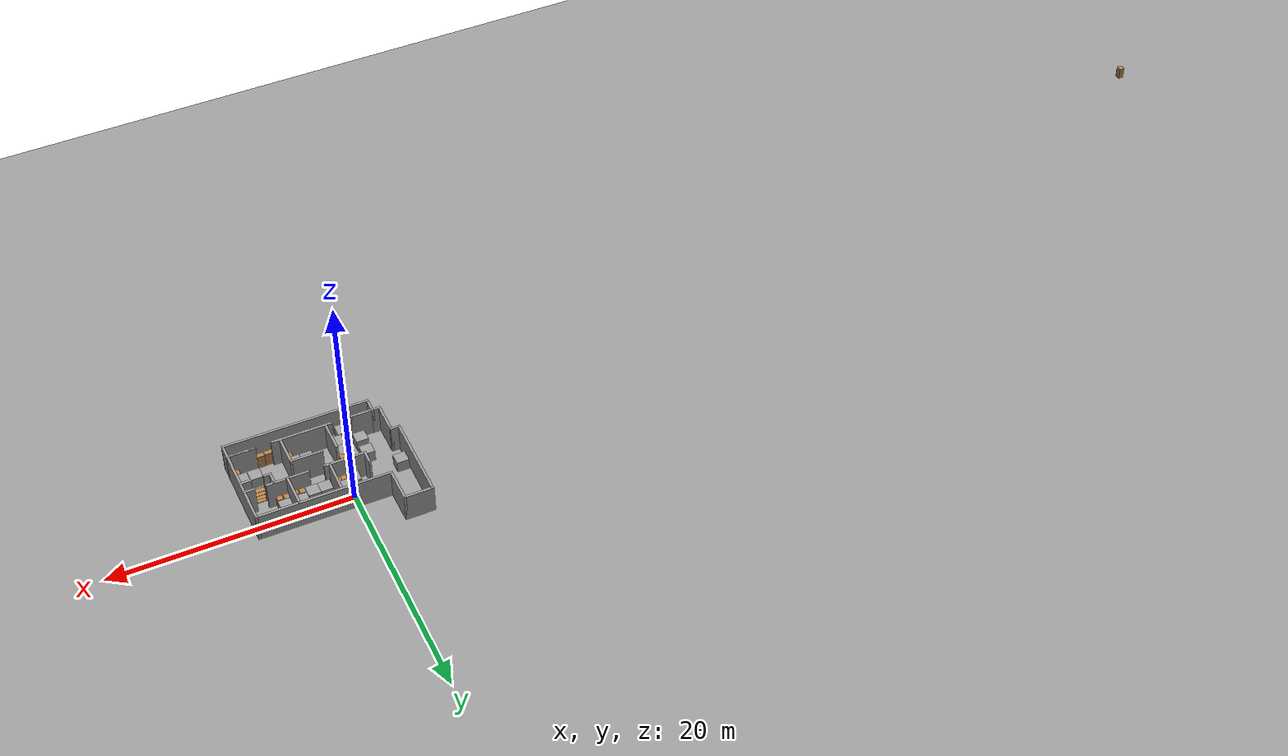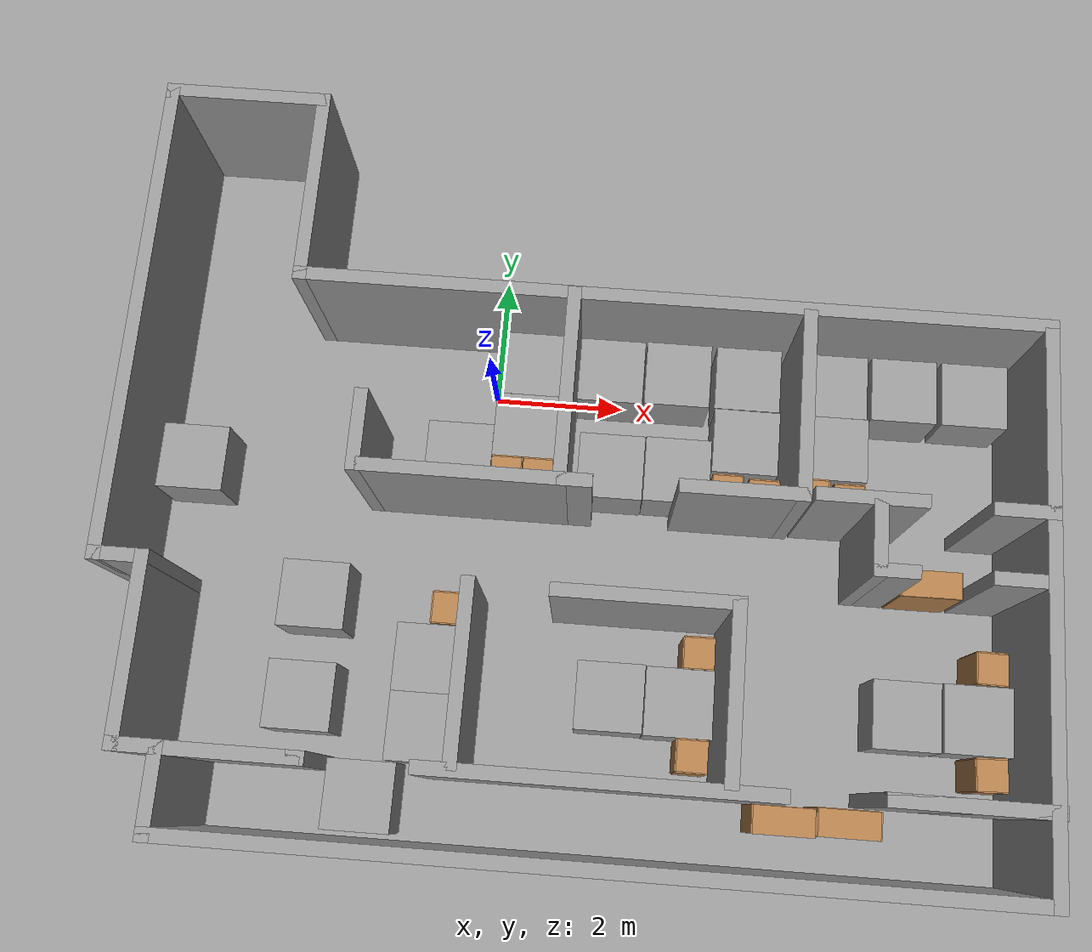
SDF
<sdf version="1.4">
 <world name="default">
  <light name="sun" type="directional">
   <pose>0 0 10 0 -0 0</pose>
   <diffuse>0.8 0.8 0.8 1</diffuse>
   <specular>0.2 0.2 0.2 1</specular>
   <attenuation>
    <range>1000</range>
    <constant>0.9</constant>
    <linear>0.01</linear>
    <quadratic>0.001</quadratic>
   </attenuation>
   <direction>0.5 0.1 -0.9</direction>
  </light>
  <scene><ambient>0.4 0.4 0.4 1</ambient><background>0.7 0.7 0.7 1</background><shadows>1</shadows></scene>
  <physics type="ode">
   <max_step_size>0.01</max_step_size>
   <real_time_factor>1</real_time_factor>
   <real_time_update_rate>100</real_time_update_rate>
   <gravity>0 0 -9.8</gravity>
  </physics>
  <model name="ground_plane_0">
   <static>1</static>
   <link name="link">
    <collision name="collision">
     <geometry><plane><normal>0 0 1</normal><size>100 100</size></plane></geometry>
     <surface><friction><ode><mu>100</mu><mu2>50</mu2></ode></friction></surface>
    </collision>
    <visual name="visual">
     <cast_shadows>0</cast_shadows>
     <geometry><plane><normal>0 0 1</normal><size>100 100</size></plane></geometry>
     <material>
      <script><uri>file://media/materials/scripts/gazebo.material</uri><name>Gazebo/Grey</name></script>
     </material>
    </visual>
    <velocity_decay><linear>0</linear><angular>0</angular></velocity_decay>
   </link>
   <pose>0.497681 0 0 0 -0 0</pose>
  </model>
  <spherical_coordinates>
   <surface_model>EARTH_WGS84</surface_model>
   <latitude_deg>0</latitude_deg>
   <longitude_deg>0</longitude_deg>
   <elevation>0</elevation>
   <heading_deg>0</heading_deg>
  </spherical_coordinates>
  <model name="roy1_0">
   <link name="Wall_14">
    <collision name="Wall_14_Collision">
     <geometry><box><size>7.30611 0.2 2.5</size></box></geometry>
     <pose>0 0 1.25 0 -0 0</pose>
    </collision>
    <visual name="Wall_14_Visual">
     <pose>0 0 1.25 0 -0 0</pose>
     <geometry><box><size>7.30611 0.2 2.5</size></box></geometry>
     <material>
      <script><uri>file://media/materials/scripts/gazebo.material</uri><name>Gazebo/Grey</name></script>
     </material>
    </visual>
    <velocity_decay><linear>0</linear><angular>0</angular></velocity_decay>
    <pose>-11.6774 0.500575 0 0 0 -1.5708</pose>
   </link>
   <link name="Wall_15">
    <collision name="Wall_15_Collision">
     <geometry><box><size>0.869322 0.2 2.5</size></box></geometry>
     <pose>0 0 1.25 0 -0 0</pose>
    </collision>
    <visual name="Wall_15_Visual">
     <pose>0 0 1.25 0 -0 0</pose>
     <geometry><box><size>0.869322 0.2 2.5</size></box></geometry>
     <material>
      <script><uri>file://media/materials/scripts/gazebo.material</uri><name>Gazebo/Grey</name></script>
     </material>
    </visual>
    <velocity_decay><linear>0</linear><angular>0</angular></velocity_decay>
    <pose>-11.3432 -3.05248 0 0 -0 0</pose>
   </link>
   <link name="Wall_16">
    <collision name="Wall_16_Collision">
     <geometry><box><size>2.73287 0.2 2.5</size></box></geometry>
     <pose>0 0 1.25 0 -0 0</pose>
    </collision>
    <visual name="Wall_16_Visual">
     <pose>0 0 1.25 0 -0 0</pose>
     <geometry><box><size>2.73287 0.2 2.5</size></box></geometry>
     <material>
      <script><uri>file://media/materials/scripts/gazebo.material</uri><name>Gazebo/Grey</name></script>
     </material>
    </visual>
    <velocity_decay><linear>0</linear><angular>0</angular></velocity_decay>
    <pose>-11.009 -4.31891 0 0 0 -1.5708</pose>
   </link>
   <link name="Wall_17">
    <collision name="Wall_17_Collision">
     <geometry><box><size>0.798039 0.2 2.5</size></box></geometry>
     <pose>0 0 1.25 0 -0 0</pose>
    </collision>
    <visual name="Wall_17_Visual">
     <pose>0 0 1.25 0 -0 0</pose>
     <geometry><box><size>0.798039 0.2 2.5</size></box></geometry>
     <material>
      <script><uri>file://media/materials/scripts/gazebo.material</uri><name>Gazebo/Grey</name></script>
     </material>
    </visual>
    <velocity_decay><linear>0</linear><angular>0</angular></velocity_decay>
    <pose>-10.71 -5.58535 0 0 -0 0</pose>
   </link>
   <link name="Wall_18">
    <collision name="Wall_18_Collision">
     <geometry><box><size>1.32572 0.2 2.5</size></box></geometry>
     <pose>0 0 1.25 0 -0 0</pose>
    </collision>
    <visual name="Wall_18_Visual">
     <pose>0 0 1.25 0 -0 0</pose>
     <geometry><box><size>1.32572 0.2 2.5</size></box></geometry>
     <material>
      <script><uri>file://media/materials/scripts/gazebo.material</uri><name>Gazebo/Grey</name></script>
     </material>
    </visual>
    <velocity_decay><linear>0</linear><angular>0</angular></velocity_decay>
    <pose>-10.411 -6.14821 0 0 0 -1.5708</pose>
   </link>
   <link name="Wall_19">
    <collision name="Wall_19_Collision">
     <geometry><box><size>12.1261 0.2 2.5</size></box></geometry>
     <pose>0 0 1.25 0 -0 0</pose>
    </collision>
    <visual name="Wall_19_Visual">
     <pose>0 0 1.25 0 -0 0</pose>
     <geometry><box><size>12.1261 0.2 2.5</size></box></geometry>
     <material>
      <script><uri>file://media/materials/scripts/gazebo.material</uri><name>Gazebo/Grey</name></script>
     </material>
    </visual>
    <velocity_decay><linear>0</linear><angular>0</angular></velocity_decay>
    <pose>-4.44816 -6.71107 0 0 -0 0</pose>
   </link>
   <link name="Wall_20">
    <collision name="Wall_20_Collision">
     <geometry><box><size>8.18558 0.2 2.5</size></box></geometry>
     <pose>0 0 1.25 0 -0 0</pose>
    </collision>
    <visual name="Wall_20_Visual">
     <pose>0 0 1.25 0 -0 0</pose>
     <geometry><box><size>8.18558 0.2 2.5</size></box></geometry>
     <material>
      <script><uri>file://media/materials/scripts/gazebo.material</uri><name>Gazebo/Grey</name></script>
     </material>
    </visual>
    <velocity_decay><linear>0</linear><angular>0</angular></velocity_decay>
    <pose>1.51464 -2.71828 0 0 -0 1.5708</pose>
   </link>
   <link name="Wall_21">
    <collision name="Wall_21_Collision">
     <geometry><box><size>11.1059 0.2 2.5</size></box></geometry>
     <pose>0 0 1.25 0 -0 0</pose>
    </collision>
    <visual name="Wall_21_Visual">
     <pose>0 0 1.25 0 -0 0</pose>
     <geometry><box><size>11.1059 0.2 2.5</size></box></geometry>
     <material>
      <script><uri>file://media/materials/scripts/gazebo.material</uri><name>Gazebo/Grey</name></script>
     </material>
    </visual>
    <velocity_decay><linear>0</linear><angular>0</angular></velocity_decay>
    <pose>-3.93807 1.27451 0 0 -0 3.14159</pose>
   </link>
   <link name="Wall_22">
    <collision name="Wall_22_Collision">
     <geometry><box><size>3.0143 0.2 2.5</size></box></geometry>
     <pose>0 0 1.25 0 -0 0</pose>
    </collision>
    <visual name="Wall_22_Visual">
     <pose>0 0 1.25 0 -0 0</pose>
     <geometry><box><size>3.0143 0.2 2.5</size></box></geometry>
     <material>
      <script><uri>file://media/materials/scripts/gazebo.material</uri><name>Gazebo/Grey</name></script>
     </material>
    </visual>
    <velocity_decay><linear>0</linear><angular>0</angular></velocity_decay>
    <pose>-9.39078 2.68166 0 0 -0 1.5708</pose>
   </link>
   <link name="Wall_23">
    <collision name="Wall_23_Collision">
     <geometry><box><size>2.48662 0.2 2.5</size></box></geometry>
     <pose>0 0 1.25 0 -0 0</pose>
    </collision>
    <visual name="Wall_23_Visual">
     <pose>0 0 1.25 0 -0 0</pose>
     <geometry><box><size>2.48662 0.2 2.5</size></box></geometry>
     <material>
      <script><uri>file://media/materials/scripts/gazebo.material</uri><name>Gazebo/Grey</name></script>
     </material>
    </visual>
    <velocity_decay><linear>0</linear><angular>0</angular></velocity_decay>
    <pose>-10.5341 4.08881 0 0 -0 3.14159</pose>
   </link>
   <link name="Wall_24">
    <collision name="Wall_24_Collision">
     <geometry><box><size>0.235179 0.2 2.5</size></box></geometry>
     <pose>0 0 1.25 0 -0 0</pose>
    </collision>
    <visual name="Wall_24_Visual">
     <pose>0 0 1.25 0 -0 0</pose>
     <geometry><box><size>0.235179 0.2 2.5</size></box></geometry>
     <material>
      <script><uri>file://media/materials/scripts/gazebo.material</uri><name>Gazebo/Grey</name></script>
     </material>
    </visual>
    <velocity_decay><linear>0</linear><angular>0</angular></velocity_decay>
    <pose>-11.6774 4.07122 0 0 0 -1.5708</pose>
   </link>
   <link name="Wall_26">
    <collision name="Wall_26_Collision">
     <geometry><box><size>2.98371 0.2 2.5</size></box></geometry>
     <pose>0 0 1.25 0 -0 0</pose>
    </collision>
    <visual name="Wall_26_Visual">
     <pose>0 0 1.25 0 -0 0</pose>
     <geometry><box><size>2.98371 0.2 2.5</size></box></geometry>
     <material>
      <script><uri>file://media/materials/scripts/gazebo.material</uri><name>Gazebo/Grey</name></script>
     </material>
    </visual>
    <velocity_decay><linear>0</linear><angular>0</angular></velocity_decay>
    <pose>-5.37546 -0.128198 0 0 0 -1.5708</pose>
   </link>
   <link name="Wall_27">
    <collision name="Wall_27_Collision">
     <geometry><box><size>3.10607 0.2 2.5</size></box></geometry>
     <pose>0 0 1.25 0 -0 0</pose>
    </collision>
    <visual name="Wall_27_Visual">
     <pose>0 0 1.25 0 -0 0</pose>
     <geometry><box><size>3.10607 0.2 2.5</size></box></geometry>
     <material>
      <script><uri>file://media/materials/scripts/gazebo.material</uri><name>Gazebo/Grey</name></script>
     </material>
    </visual>
    <velocity_decay><linear>0</linear><angular>0</angular></velocity_decay>
    <pose>-6.8285 -1.52005 0 0 -0 3.14159</pose>
   </link>
   <link name="Wall_28">
    <collision name="Wall_28_Collision">
     <geometry><box><size>1.20948 0.2 2.5</size></box></geometry>
     <pose>0 0 1.25 0 -0 0</pose>
    </collision>
    <visual name="Wall_28_Visual">
     <pose>0 0 1.25 0 -0 0</pose>
     <geometry><box><size>1.20948 0.2 2.5</size></box></geometry>
     <material>
      <script><uri>file://media/materials/scripts/gazebo.material</uri><name>Gazebo/Grey</name></script>
     </material>
    </visual>
    <velocity_decay><linear>0</linear><angular>0</angular></velocity_decay>
    <pose>-8.28153 -1.01531 0 0 -0 1.5708</pose>
   </link>
   <link name="Wall_30">
    <collision name="Wall_30_Collision">
     <geometry><box><size>0.505902 0.2 2.5</size></box></geometry>
     <pose>0 0 1.25 0 -0 0</pose>
    </collision>
    <visual name="Wall_30_Visual">
     <pose>0 0 1.25 0 -0 0</pose>
     <geometry><box><size>0.505902 0.2 2.5</size></box></geometry>
     <material>
      <script><uri>file://media/materials/scripts/gazebo.material</uri><name>Gazebo/Grey</name></script>
     </material>
    </visual>
    <velocity_decay><linear>0</linear><angular>0</angular></velocity_decay>
    <pose>-5.16133 -1.52005 0 0 -0 0</pose>
   </link>
   <link name="Wall_32">
    <collision name="Wall_32_Collision">
     <geometry><box><size>2.95329 0.2 2.5</size></box></geometry>
     <pose>0 0 1.25 0 -0 0</pose>
    </collision>
    <visual name="Wall_32_Visual">
     <pose>0 0 1.25 0 -0 0</pose>
     <geometry><box><size>2.95329 0.2 2.5</size></box></geometry>
     <material>
      <script><uri>file://media/materials/scripts/gazebo.material</uri><name>Gazebo/Grey</name></script>
     </material>
    </visual>
    <velocity_decay><linear>0</linear><angular>0</angular></velocity_decay>
    <pose>-1.94935 -0.112818 0 0 0 -1.5708</pose>
   </link>
   <link name="Wall_33">
    <collision name="Wall_33_Collision">
     <geometry><box><size>1.85187 0.2 2.5</size></box></geometry>
     <pose>0 0 1.25 0 -0 0</pose>
    </collision>
    <visual name="Wall_33_Visual">
     <pose>0 0 1.25 0 -0 0</pose>
     <geometry><box><size>1.85187 0.2 2.5</size></box></geometry>
     <material>
      <script><uri>file://media/materials/scripts/gazebo.material</uri><name>Gazebo/Grey</name></script>
     </material>
    </visual>
    <velocity_decay><linear>0</linear><angular>0</angular></velocity_decay>
    <pose>-2.77529 -1.48946 0 0 -0 3.14159</pose>
   </link>
   <link name="Wall_38">
    <collision name="Wall_38_Collision">
     <geometry><box><size>1.6 0.2 2.5</size></box></geometry>
     <pose>0 0 1.25 0 -0 0</pose>
    </collision>
    <visual name="Wall_38_Visual">
     <pose>0 0 1.25 0 -0 0</pose>
     <geometry><box><size>1.6 0.2 2.5</size></box></geometry>
     <material>
      <script><uri>file://media/materials/scripts/gazebo.material</uri><name>Gazebo/Grey</name></script>
     </material>
    </visual>
    <velocity_decay><linear>0</linear><angular>0</angular></velocity_decay>
    <pose>-1.00106 -1.45887 0 0 -0 0</pose>
   </link>
   <link name="Wall_40">
    <collision name="Wall_40_Collision">
     <geometry><box><size>0.934165 0.2 2.5</size></box></geometry>
     <pose>0 0 1.25 0 -0 0</pose>
    </collision>
    <visual name="Wall_40_Visual">
     <pose>0 0 1.25 0 -0 0</pose>
     <geometry><box><size>0.934165 0.2 2.5</size></box></geometry>
     <material>
      <script><uri>file://media/materials/scripts/gazebo.material</uri><name>Gazebo/Grey</name></script>
     </material>
    </visual>
    <velocity_decay><linear>0</linear><angular>0</angular></velocity_decay>
    <pose>1.14026 -1.48946 0 0 -0 0</pose>
   </link>
   <link name="Wall_42">
    <collision name="Wall_42_Collision">
     <geometry><box><size>1.17889 0.2 2.5</size></box></geometry>
     <pose>0 0 1.25 0 -0 0</pose>
    </collision>
    <visual name="Wall_42_Visual">
     <pose>0 0 1.25 0 -0 0</pose>
     <geometry><box><size>1.17889 0.2 2.5</size></box></geometry>
     <material>
      <script><uri>file://media/materials/scripts/gazebo.material</uri><name>Gazebo/Grey</name></script>
     </material>
    </visual>
    <velocity_decay><linear>0</linear><angular>0</angular></velocity_decay>
    <pose>-0.878696 -1.97891 0 0 0 -1.5708</pose>
   </link>
   <link name="Wall_43">
    <collision name="Wall_43_Collision">
     <geometry><box><size>0.658853 0.2 2.5</size></box></geometry>
     <pose>0 0 1.25 0 -0 0</pose>
    </collision>
    <visual name="Wall_43_Visual">
     <pose>0 0 1.25 0 -0 0</pose>
     <geometry><box><size>0.658853 0.2 2.5</size></box></geometry>
     <material>
      <script><uri>file://media/materials/scripts/gazebo.material</uri><name>Gazebo/Grey</name></script>
     </material>
    </visual>
    <velocity_decay><linear>0</linear><angular>0</angular></velocity_decay>
    <pose>-0.64927 -2.46835 0 0 -0 0</pose>
   </link>
   <link name="Wall_45">
    <collision name="Wall_45_Collision">
     <geometry><box><size>0.903575 0.2 2.5</size></box></geometry>
     <pose>0 0 1.25 0 -0 0</pose>
    </collision>
    <visual name="Wall_45_Visual">
     <pose>0 0 1.25 0 -0 0</pose>
     <geometry><box><size>0.903575 0.2 2.5</size></box></geometry>
     <material>
      <script><uri>file://media/materials/scripts/gazebo.material</uri><name>Gazebo/Grey</name></script>
     </material>
    </visual>
    <velocity_decay><linear>0</linear><angular>0</angular></velocity_decay>
    <pose>1.12496 -2.46835 0 0 -0 0</pose>
   </link>
   <link name="Wall_47">
    <collision name="Wall_47_Collision">
     <geometry><box><size>2.70858 0.2 2.5</size></box></geometry>
     <pose>0 0 1.25 0 -0 0</pose>
    </collision>
    <visual name="Wall_47_Visual">
     <pose>0 0 1.25 0 -0 0</pose>
     <geometry><box><size>2.70858 0.2 2.5</size></box></geometry>
     <material>
      <script><uri>file://media/materials/scripts/gazebo.material</uri><name>Gazebo/Grey</name></script>
     </material>
    </visual>
    <velocity_decay><linear>0</linear><angular>0</angular></velocity_decay>
    <pose>-4.02958 -3.08015 0 0 -0 0</pose>
   </link>
   <link name="Wall_48">
    <collision name="Wall_48_Collision">
     <geometry><box><size>2.58604 0.2 2.5</size></box></geometry>
     <pose>0 0 1.25 0 -0 0</pose>
    </collision>
    <visual name="Wall_48_Visual">
     <pose>0 0 1.25 0 -0 0</pose>
     <geometry><box><size>2.58604 0.2 2.5</size></box></geometry>
     <material>
      <script><uri>file://media/materials/scripts/gazebo.material</uri><name>Gazebo/Grey</name></script>
     </material>
    </visual>
    <velocity_decay><linear>0</linear><angular>0</angular></velocity_decay>
    <pose>-2.77529 -4.27317 0 0 0 -1.5708</pose>
   </link>
   <link name="Wall_50">
    <collision name="Wall_50_Collision">
     <geometry><box><size>2.61663 0.2 2.5</size></box></geometry>
     <pose>0 0 1.25 0 -0 0</pose>
    </collision>
    <visual name="Wall_50_Visual">
     <pose>0 0 1.25 0 -0 0</pose>
     <geometry><box><size>2.61663 0.2 2.5</size></box></geometry>
     <material>
      <script><uri>file://media/materials/scripts/gazebo.material</uri><name>Gazebo/Grey</name></script>
     </material>
    </visual>
    <velocity_decay><linear>0</linear><angular>0</angular></velocity_decay>
    <pose>-6.5073 -4.28847 0 0 0 -1.5708</pose>
   </link>
   <link name="Wall_54">
    <collision name="Wall_54_Collision">
     <geometry><box><size>2.00482 0.2 2.5</size></box></geometry>
     <pose>0 0 1.25 0 -0 0</pose>
    </collision>
    <visual name="Wall_54_Visual">
     <pose>0 0 1.25 0 -0 0</pose>
     <geometry><box><size>2.00482 0.2 2.5</size></box></geometry>
     <material>
      <script><uri>file://media/materials/scripts/gazebo.material</uri><name>Gazebo/Grey</name></script>
     </material>
    </visual>
    <velocity_decay><linear>0</linear><angular>0</angular></velocity_decay>
    <pose>-9.48985 -5.58855 0 0 -0 0</pose>
   </link>
   <link name="Wall_55">
    <collision name="Wall_55_Collision">
     <geometry><box><size>0.26118 0.2 2.5</size></box></geometry>
     <pose>0 0 1.25 0 -0 0</pose>
    </collision>
    <visual name="Wall_55_Visual">
     <pose>0 0 1.25 0 -0 0</pose>
     <geometry><box><size>0.26118 0.2 2.5</size></box></geometry>
     <material>
      <script><uri>file://media/materials/scripts/gazebo.material</uri><name>Gazebo/Grey</name></script>
     </material>
    </visual>
    <velocity_decay><linear>0</linear><angular>0</angular></velocity_decay>
    <pose>-8.55684 -5.58855 0 0 -0 0</pose>
   </link>
   <link name="Wall_57">
    <collision name="Wall_57_Collision">
     <geometry><box><size>5.03326 0.2 2.5</size></box></geometry>
     <pose>0 0 1.25 0 -0 0</pose>
    </collision>
    <visual name="Wall_57_Visual">
     <pose>0 0 1.25 0 -0 0</pose>
     <geometry><box><size>5.03326 0.2 2.5</size></box></geometry>
     <material>
      <script><uri>file://media/materials/scripts/gazebo.material</uri><name>Gazebo/Grey</name></script>
     </material>
    </visual>
    <velocity_decay><linear>0</linear><angular>0</angular></velocity_decay>
    <pose>-4.51893 -5.58855 0 0 -0 0</pose>
   </link>
   <link name="Wall_62">
    <collision name="Wall_62_Collision">
     <geometry><box><size>2.37191 0.2 2.5</size></box></geometry>
     <pose>0 0 1.25 0 -0 0</pose>
    </collision>
    <visual name="Wall_62_Visual">
     <pose>0 0 1.25 0 -0 0</pose>
     <geometry><box><size>2.37191 0.2 2.5</size></box></geometry>
     <material>
      <script><uri>file://media/materials/scripts/gazebo.material</uri><name>Gazebo/Grey</name></script>
     </material>
    </visual>
    <velocity_decay><linear>0</linear><angular>0</angular></velocity_decay>
    <pose>0.451979 -5.52737 0 0 -0 0</pose>
   </link>
   <link name="Wall_63">
    <collision name="Wall_63_Collision">
     <geometry><box><size>2.37191 0.2 2.5</size></box></geometry>
     <pose>0 0 1.25 0 -0 0</pose>
    </collision>
    <visual name="Wall_63_Visual">
     <pose>0 0 1.25 0 -0 0</pose>
     <geometry><box><size>2.37191 0.2 2.5</size></box></geometry>
     <material>
      <script><uri>file://media/materials/scripts/gazebo.material</uri><name>Gazebo/Grey</name></script>
     </material>
    </visual>
    <velocity_decay><linear>0</linear><angular>0</angular></velocity_decay>
    <pose>0.451979 -5.52737 0 0 -0 3.14159</pose>
   </link>
   <static>1</static>
   <pose>6.55073 -0.34156 0 0 -0 0</pose>
  </model>
  <model name="unit_box_4_0">
   <pose>-2.39893 -5.00271 0.5 0 -0 7e-06</pose>
   <link name="link">
    <inertial>
     <mass>1</mass>
     <inertia><ixx>1</ixx><ixy>0</ixy><ixz>0</ixz><iyy>1</iyy><iyz>0</iyz><izz>1</izz></inertia>
    </inertial>
    <collision name="collision"><geometry><box><size>0.744112 0.760024 1</size></box></geometry></collision>
    <visual name="visual">
     <geometry><box><size>1 1 1</size></box></geometry>
     <material>
      <script><uri>file://media/materials/scripts/gazebo.material</uri><name>Gazebo/Grey</name></script>
     </material>
    </visual>
    <velocity_decay><linear>0</linear><angular>0</angular></velocity_decay>
   </link>
   <static>0</static>
  </model>
  <model name="unit_box_5_1">
   <pose>-2.3795 -3.51297 0.5 0 -0 8e-06</pose>
   <link name="link">
    <inertial>
     <mass>1</mass>
     <inertia><ixx>1</ixx><ixy>0</ixy><ixz>0</ixz><iyy>1</iyy><iyz>0</iyz><izz>1</izz></inertia>
    </inertial>
    <collision name="collision"><geometry><box><size>0.763692 0.765523 1</size></box></geometry></collision>
    <visual name="visual">
     <geometry><box><size>1 1 1</size></box></geometry>
     <material>
      <script><uri>file://media/materials/scripts/gazebo.material</uri><name>Gazebo/Grey</name></script>
     </material>
    </visual>
    <velocity_decay><linear>0</linear><angular>0</angular></velocity_decay>
   </link>
   <static>0</static>
  </model>
  <model name="unit_box_1_2">
   <pose>2.1116 -4.68526 0.5 0 -0 0.002135</pose>
   <link name="link">
    <inertial>
     <mass>1</mass>
     <inertia><ixx>1</ixx><ixy>0</ixy><ixz>0</ixz><iyy>1</iyy><iyz>0</iyz><izz>1</izz></inertia>
    </inertial>
    <collision name="collision"><geometry><box><size>1 1 1</size></box></geometry></collision>
    <visual name="visual">
     <geometry><box><size>1 1 1</size></box></geometry>
     <material>
      <script><uri>file://media/materials/scripts/gazebo.material</uri><name>Gazebo/Grey</name></script>
     </material>
    </visual>
    <velocity_decay><linear>0</linear><angular>0</angular></velocity_decay>
   </link>
   <static>0</static>
  </model>
  <model name="unit_box_2">
   <pose>-0.57904 -4.33008 0.5 0 -0 1.1e-05</pose>
   <link name="link">
    <inertial>
     <mass>1</mass>
     <inertia><ixx>1</ixx><ixy>0</ixy><ixz>0</ixz><iyy>1</iyy><iyz>0</iyz><izz>1</izz></inertia>
    </inertial>
    <collision name="collision"><geometry><box><size>1 1 1</size></box></geometry></collision>
    <visual name="visual">
     <geometry><box><size>1 1 1</size></box></geometry>
     <material>
      <script><uri>file://media/materials/scripts/gazebo.material</uri><name>Gazebo/Grey</name></script>
     </material>
    </visual>
    <velocity_decay><linear>0</linear><angular>0</angular></velocity_decay>
   </link>
   <static>0</static>
  </model>
  <model name="unit_box_3_0">
   <pose>0.558438 0.317764 0.5 0 0 -0.001057</pose>
   <link name="link">
    <inertial>
     <mass>1</mass>
     <inertia><ixx>1</ixx><ixy>0</ixy><ixz>0</ixz><iyy>1</iyy><iyz>0</iyz><izz>1</izz></inertia>
    </inertial>
    <collision name="collision"><geometry><box><size>1 1 1</size></box></geometry></collision>
    <visual name="visual">
     <geometry><box><size>1 1 1</size></box></geometry>
     <material>
      <script><uri>file://media/materials/scripts/gazebo.material</uri><name>Gazebo/Grey</name></script>
     </material>
    </visual>
    <velocity_decay><linear>0</linear><angular>0</angular></velocity_decay>
   </link>
   <static>0</static>
  </model>
  <model name="unit_box_5_0">
   <pose>0.560372 -0.682679 0.5 0 -0 1.57055</pose>
   <link name="link">
    <inertial>
     <mass>1</mass>
     <inertia><ixx>1</ixx><ixy>0</ixy><ixz>0</ixz><iyy>1</iyy><iyz>0</iyz><izz>1</izz></inertia>
    </inertial>
    <collision name="collision"><geometry><box><size>1 1 1</size></box></geometry></collision>
    <visual name="visual">
     <geometry><box><size>1 1 1</size></box></geometry>
     <material>
      <script><uri>file://media/materials/scripts/gazebo.material</uri><name>Gazebo/Grey</name></script>
     </material>
    </visual>
    <velocity_decay><linear>0</linear><angular>0</angular></velocity_decay>
   </link>
   <static>0</static>
  </model>
  <model name="unit_box_7">
   <pose>2.82216 0.318267 0.5 0 0 -2e-06</pose>
   <link name="link">
    <inertial>
     <mass>1</mass>
     <inertia><ixx>1</ixx><ixy>0</ixy><ixz>0</ixz><iyy>1</iyy><iyz>0</iyz><izz>1</izz></inertia>
    </inertial>
    <collision name="collision"><geometry><box><size>1 1 1</size></box></geometry></collision>
    <visual name="visual">
     <geometry><box><size>1 1 1</size></box></geometry>
     <material>
      <script><uri>file://media/materials/scripts/gazebo.material</uri><name>Gazebo/Grey</name></script>
     </material>
    </visual>
    <velocity_decay><linear>0</linear><angular>0</angular></velocity_decay>
   </link>
   <static>0</static>
  </model>
  <model name="unit_box_8_0">
   <pose>3.90619 0.318266 0.5 0 0 -3e-06</pose>
   <link name="link">
    <inertial>
     <mass>1</mass>
     <inertia><ixx>1</ixx><ixy>0</ixy><ixz>0</ixz><iyy>1</iyy><iyz>0</iyz><izz>1</izz></inertia>
    </inertial>
    <collision name="collision"><geometry><box><size>1 1 1</size></box></geometry></collision>
    <visual name="visual">
     <geometry><box><size>1 1 1</size></box></geometry>
     <material>
      <script><uri>file://media/materials/scripts/gazebo.material</uri><name>Gazebo/Grey</name></script>
     </material>
    </visual>
    <velocity_decay><linear>0</linear><angular>0</angular></velocity_decay>
   </link>
   <static>0</static>
  </model>
  <model name="unit_box_9">
   <pose>6.31337 0.31804 0.5 0 0 -1e-06</pose>
   <link name="link">
    <inertial>
     <mass>1</mass>
     <inertia><ixx>1</ixx><ixy>0</ixy><ixz>0</ixz><iyy>1</iyy><iyz>0</iyz><izz>1</izz></inertia>
    </inertial>
    <collision name="collision"><geometry><box><size>1 1 1</size></box></geometry></collision>
    <visual name="visual">
     <geometry><box><size>1 1 1</size></box></geometry>
     <material>
      <script><uri>file://media/materials/scripts/gazebo.material</uri><name>Gazebo/Grey</name></script>
     </material>
    </visual>
    <velocity_decay><linear>0</linear><angular>0</angular></velocity_decay>
   </link>
   <static>0</static>
  </model>
  <model name="unit_box_10">
   <pose>7.39302 0.318011 0.5 0 0 -1e-06</pose>
   <link name="link">
    <inertial>
     <mass>1</mass>
     <inertia><ixx>1</ixx><ixy>0</ixy><ixz>0</ixz><iyy>1</iyy><iyz>0</iyz><izz>1</izz></inertia>
    </inertial>
    <collision name="collision"><geometry><box><size>1 1 1</size></box></geometry></collision>
    <visual name="visual">
     <geometry><box><size>1 1 1</size></box></geometry>
     <material>
      <script><uri>file://media/materials/scripts/gazebo.material</uri><name>Gazebo/Grey</name></script>
     </material>
    </visual>
    <velocity_decay><linear>0</linear><angular>0</angular></velocity_decay>
   </link>
   <static>0</static>
  </model>
  <model name="unit_box_11">
   <pose>5.24591 0.307406 0.5 0 -0 0.001323</pose>
   <link name="link">
    <inertial>
     <mass>1</mass>
     <inertia><ixx>1</ixx><ixy>0</ixy><ixz>0</ixz><iyy>1</iyy><iyz>0</iyz><izz>1</izz></inertia>
    </inertial>
    <collision name="collision"><geometry><box><size>1 1 1</size></box></geometry></collision>
    <visual name="visual">
     <geometry><box><size>1 1 1</size></box></geometry>
     <material>
      <script><uri>file://media/materials/scripts/gazebo.material</uri><name>Gazebo/Grey</name></script>
     </material>
    </visual>
    <velocity_decay><linear>0</linear><angular>0</angular></velocity_decay>
   </link>
   <static>0</static>
  </model>
  <model name="unit_box_14">
   <pose>3.12567 -4.69625 0.497132 -0.000574 -0.00035 0.004994</pose>
   <link name="link">
    <inertial>
     <mass>1</mass>
     <inertia><ixx>1</ixx><ixy>0</ixy><ixz>0</ixz><iyy>1</iyy><iyz>0</iyz><izz>1</izz></inertia>
    </inertial>
    <collision name="collision"><geometry><box><size>1 1 1</size></box></geometry></collision>
    <visual name="visual">
     <geometry><box><size>1 1 1</size></box></geometry>
     <material>
      <script><uri>file://media/materials/scripts/gazebo.material</uri><name>Gazebo/Grey</name></script>
     </material>
    </visual>
    <velocity_decay><linear>0</linear><angular>0</angular></velocity_decay>
   </link>
   <static>0</static>
  </model>
  <model name="cabinet">
   <static>1</static>
   <link name="cabinet_bottom_plate">
    <inertial>
     <pose>0 0 -1 0 -0 0</pose>
     <inertia><ixx>2.05</ixx><ixy>0</ixy><ixz>0</ixz><iyy>2.05</iyy><iyz>0</iyz><izz>2.05</izz></inertia>
     <mass>25</mass>
    </inertial>
    <collision name="cabinet_bottom_plate_geom">
     <pose>0 0 0.01 0 -0 0</pose>
     <geometry><box><size>0.45 0.45 0.02</size></box></geometry>
    </collision>
    <visual name="cabinet_bottom_plate_geom_visual">
     <pose>0 0 0.01 0 -0 0</pose>
     <geometry><box><size>0.45 0.45 0.02</size></box></geometry>
     <material>
      <script><uri>file://media/materials/scripts/gazebo.material</uri><name>Gazebo/Wood</name></script>
     </material>
    </visual>
    <collision name="cabinet_bottom_plate_geom_cabinet_back_plate">
     <pose>0.235 0 0.51 0 -0 0</pose>
     <geometry><box><size>0.02 0.45 1.02</size></box></geometry>
    </collision>
    <visual name="cabinet_bottom_plate_geom_cabinet_back_plate_visual">
     <pose>0.235 0 0.51 0 -0 0</pose>
     <geometry><box><size>0.02 0.45 1.02</size></box></geometry>
     <material>
      <script><uri>file://media/materials/scripts/gazebo.material</uri><name>Gazebo/Wood</name></script>
     </material>
    </visual>
    <collision name="cabinet_bottom_plate_geom_cabinet_left_plate">
     <pose>0 0.235 0.51 0 -0 0</pose>
     <geometry><box><size>0.45 0.02 1.02</size></box></geometry>
    </collision>
    <visual name="cabinet_bottom_plate_geom_cabinet_left_plate_visual">
     <pose>0 0.235 0.51 0 -0 0</pose>
     <geometry><box><size>0.45 0.02 1.02</size></box></geometry>
     <material>
      <script><uri>file://media/materials/scripts/gazebo.material</uri><name>Gazebo/Wood</name></script>
     </material>
    </visual>
    <collision name="cabinet_bottom_plate_geom_cabinet_middle_plate">
     <pose>0 0 0.51 0 -0 0</pose>
     <geometry><box><size>0.45 0.45 0.02</size></box></geometry>
    </collision>
    <visual name="cabinet_bottom_plate_geom_cabinet_middle_plate_visual">
     <pose>0 0 0.51 0 -0 0</pose>
     <geometry><box><size>0.45 0.45 0.02</size></box></geometry>
     <material>
      <script><uri>file://media/materials/scripts/gazebo.material</uri><name>Gazebo/Wood</name></script>
     </material>
    </visual>
    <collision name="cabinet_bottom_plate_geom_cabinet_right_plate">
     <pose>0 -0.235 0.51 0 -0 0</pose>
     <geometry><box><size>0.45 0.02 1.02</size></box></geometry>
    </collision>
    <visual name="cabinet_bottom_plate_geom_cabinet_right_plate_visual">
     <pose>0 -0.235 0.51 0 -0 0</pose>
     <geometry><box><size>0.45 0.02 1.02</size></box></geometry>
     <material>
      <script><uri>file://media/materials/scripts/gazebo.material</uri><name>Gazebo/Wood</name></script>
     </material>
    </visual>
    <collision name="cabinet_bottom_plate_geom_cabinet_top_plate">
     <pose>0 0 1.01 0 -0 0</pose>
     <geometry><box><size>0.45 0.45 0.02</size></box></geometry>
    </collision>
    <visual name="cabinet_bottom_plate_geom_cabinet_top_plate_visual">
     <pose>0 0 1.01 0 -0 0</pose>
     <geometry><box><size>0.45 0.45 0.02</size></box></geometry>
     <material>
      <script><uri>file://media/materials/scripts/gazebo.material</uri><name>Gazebo/Wood</name></script>
     </material>
    </visual>
    <velocity_decay><linear>0</linear><angular>0</angular></velocity_decay>
   </link>
   <pose>3.38074 -3.95771 0 0 0 -3.13001</pose>
  </model>
  <model name="cabinet_0">
   <static>1</static>
   <link name="cabinet_bottom_plate">
    <inertial>
     <pose>0 0 -1 0 -0 0</pose>
     <inertia><ixx>2.05</ixx><ixy>0</ixy><ixz>0</ixz><iyy>2.05</iyy><iyz>0</iyz><izz>2.05</izz></inertia>
     <mass>25</mass>
    </inertial>
    <collision name="cabinet_bottom_plate_geom">
     <pose>0 0 0.01 0 -0 0</pose>
     <geometry><box><size>0.45 0.45 0.02</size></box></geometry>
    </collision>
    <visual name="cabinet_bottom_plate_geom_visual">
     <pose>0 0 0.01 0 -0 0</pose>
     <geometry><box><size>0.45 0.45 0.02</size></box></geometry>
     <material>
      <script><uri>file://media/materials/scripts/gazebo.material</uri><name>Gazebo/Wood</name></script>
     </material>
    </visual>
    <collision name="cabinet_bottom_plate_geom_cabinet_back_plate">
     <pose>0.235 0 0.51 0 -0 0</pose>
     <geometry><box><size>0.02 0.45 1.02</size></box></geometry>
    </collision>
    <visual name="cabinet_bottom_plate_geom_cabinet_back_plate_visual">
     <pose>0.235 0 0.51 0 -0 0</pose>
     <geometry><box><size>0.02 0.45 1.02</size></box></geometry>
     <material>
      <script><uri>file://media/materials/scripts/gazebo.material</uri><name>Gazebo/Wood</name></script>
     </material>
    </visual>
    <collision name="cabinet_bottom_plate_geom_cabinet_left_plate">
     <pose>0 0.235 0.51 0 -0 0</pose>
     <geometry><box><size>0.45 0.02 1.02</size></box></geometry>
    </collision>
    <visual name="cabinet_bottom_plate_geom_cabinet_left_plate_visual">
     <pose>0 0.235 0.51 0 -0 0</pose>
     <geometry><box><size>0.45 0.02 1.02</size></box></geometry>
     <material>
      <script><uri>file://media/materials/scripts/gazebo.material</uri><name>Gazebo/Wood</name></script>
     </material>
    </visual>
    <collision name="cabinet_bottom_plate_geom_cabinet_middle_plate">
     <pose>0 0 0.51 0 -0 0</pose>
     <geometry><box><size>0.45 0.45 0.02</size></box></geometry>
    </collision>
    <visual name="cabinet_bottom_plate_geom_cabinet_middle_plate_visual">
     <pose>0 0 0.51 0 -0 0</pose>
     <geometry><box><size>0.45 0.45 0.02</size></box></geometry>
     <material>
      <script><uri>file://media/materials/scripts/gazebo.material</uri><name>Gazebo/Wood</name></script>
     </material>
    </visual>
    <collision name="cabinet_bottom_plate_geom_cabinet_right_plate">
     <pose>0 -0.235 0.51 0 -0 0</pose>
     <geometry><box><size>0.45 0.02 1.02</size></box></geometry>
    </collision>
    <visual name="cabinet_bottom_plate_geom_cabinet_right_plate_visual">
     <pose>0 -0.235 0.51 0 -0 0</pose>
     <geometry><box><size>0.45 0.02 1.02</size></box></geometry>
     <material>
      <script><uri>file://media/materials/scripts/gazebo.material</uri><name>Gazebo/Wood</name></script>
     </material>
    </visual>
    <collision name="cabinet_bottom_plate_geom_cabinet_top_plate">
     <pose>0 0 1.01 0 -0 0</pose>
     <geometry><box><size>0.45 0.45 0.02</size></box></geometry>
    </collision>
    <visual name="cabinet_bottom_plate_geom_cabinet_top_plate_visual">
     <pose>0 0 1.01 0 -0 0</pose>
     <geometry><box><size>0.45 0.45 0.02</size></box></geometry>
     <material>
      <script><uri>file://media/materials/scripts/gazebo.material</uri><name>Gazebo/Wood</name></script>
     </material>
    </visual>
    <velocity_decay><linear>0</linear><angular>0</angular></velocity_decay>
   </link>
   <pose>3.35545 -5.44222 0 0 -0 3.13235</pose>
  </model>
  <model name="cabinet_1">
   <static>1</static>
   <link name="cabinet_bottom_plate">
    <inertial>
     <pose>0 0 -1 0 -0 0</pose>
     <inertia><ixx>2.05</ixx><ixy>0</ixy><ixz>0</ixz><iyy>2.05</iyy><iyz>0</iyz><izz>2.05</izz></inertia>
     <mass>25</mass>
    </inertial>
    <collision name="cabinet_bottom_plate_geom">
     <pose>0 0 0.01 0 -0 0</pose>
     <geometry><box><size>0.45 0.45 0.02</size></box></geometry>
    </collision>
    <visual name="cabinet_bottom_plate_geom_visual">
     <pose>0 0 0.01 0 -0 0</pose>
     <geometry><box><size>0.45 0.45 0.02</size></box></geometry>
     <material>
      <script><uri>file://media/materials/scripts/gazebo.material</uri><name>Gazebo/Wood</name></script>
     </material>
    </visual>
    <collision name="cabinet_bottom_plate_geom_cabinet_back_plate">
     <pose>0.235 0 0.51 0 -0 0</pose>
     <geometry><box><size>0.02 0.45 1.02</size></box></geometry>
    </collision>
    <visual name="cabinet_bottom_plate_geom_cabinet_back_plate_visual">
     <pose>0.235 0 0.51 0 -0 0</pose>
     <geometry><box><size>0.02 0.45 1.02</size></box></geometry>
     <material>
      <script><uri>file://media/materials/scripts/gazebo.material</uri><name>Gazebo/Wood</name></script>
     </material>
    </visual>
    <collision name="cabinet_bottom_plate_geom_cabinet_left_plate">
     <pose>0 0.235 0.51 0 -0 0</pose>
     <geometry><box><size>0.45 0.02 1.02</size></box></geometry>
    </collision>
    <visual name="cabinet_bottom_plate_geom_cabinet_left_plate_visual">
     <pose>0 0.235 0.51 0 -0 0</pose>
     <geometry><box><size>0.45 0.02 1.02</size></box></geometry>
     <material>
      <script><uri>file://media/materials/scripts/gazebo.material</uri><name>Gazebo/Wood</name></script>
     </material>
    </visual>
    <collision name="cabinet_bottom_plate_geom_cabinet_middle_plate">
     <pose>0 0 0.51 0 -0 0</pose>
     <geometry><box><size>0.45 0.45 0.02</size></box></geometry>
    </collision>
    <visual name="cabinet_bottom_plate_geom_cabinet_middle_plate_visual">
     <pose>0 0 0.51 0 -0 0</pose>
     <geometry><box><size>0.45 0.45 0.02</size></box></geometry>
     <material>
      <script><uri>file://media/materials/scripts/gazebo.material</uri><name>Gazebo/Wood</name></script>
     </material>
    </visual>
    <collision name="cabinet_bottom_plate_geom_cabinet_right_plate">
     <pose>0 -0.235 0.51 0 -0 0</pose>
     <geometry><box><size>0.45 0.02 1.02</size></box></geometry>
    </collision>
    <visual name="cabinet_bottom_plate_geom_cabinet_right_plate_visual">
     <pose>0 -0.235 0.51 0 -0 0</pose>
     <geometry><box><size>0.45 0.02 1.02</size></box></geometry>
     <material>
      <script><uri>file://media/materials/scripts/gazebo.material</uri><name>Gazebo/Wood</name></script>
     </material>
    </visual>
    <collision name="cabinet_bottom_plate_geom_cabinet_top_plate">
     <pose>0 0 1.01 0 -0 0</pose>
     <geometry><box><size>0.45 0.45 0.02</size></box></geometry>
    </collision>
    <visual name="cabinet_bottom_plate_geom_cabinet_top_plate_visual">
     <pose>0 0 1.01 0 -0 0</pose>
     <geometry><box><size>0.45 0.45 0.02</size></box></geometry>
     <material>
      <script><uri>file://media/materials/scripts/gazebo.material</uri><name>Gazebo/Wood</name></script>
     </material>
    </visual>
    <velocity_decay><linear>0</linear><angular>0</angular></velocity_decay>
   </link>
   <pose>7.65336 -5.38373 0 0 0 -3.10739</pose>
  </model>
  <model name="cabinet_2">
   <static>1</static>
   <link name="cabinet_bottom_plate">
    <inertial>
     <pose>0 0 -1 0 -0 0</pose>
     <inertia><ixx>2.05</ixx><ixy>0</ixy><ixz>0</ixz><iyy>2.05</iyy><iyz>0</iyz><izz>2.05</izz></inertia>
     <mass>25</mass>
    </inertial>
    <collision name="cabinet_bottom_plate_geom">
     <pose>0 0 0.01 0 -0 0</pose>
     <geometry><box><size>0.45 0.45 0.02</size></box></geometry>
    </collision>
    <visual name="cabinet_bottom_plate_geom_visual">
     <pose>0 0 0.01 0 -0 0</pose>
     <geometry><box><size>0.45 0.45 0.02</size></box></geometry>
     <material>
      <script><uri>file://media/materials/scripts/gazebo.material</uri><name>Gazebo/Wood</name></script>
     </material>
    </visual>
    <collision name="cabinet_bottom_plate_geom_cabinet_back_plate">
     <pose>0.235 0 0.51 0 -0 0</pose>
     <geometry><box><size>0.02 0.45 1.02</size></box></geometry>
    </collision>
    <visual name="cabinet_bottom_plate_geom_cabinet_back_plate_visual">
     <pose>0.235 0 0.51 0 -0 0</pose>
     <geometry><box><size>0.02 0.45 1.02</size></box></geometry>
     <material>
      <script><uri>file://media/materials/scripts/gazebo.material</uri><name>Gazebo/Wood</name></script>
     </material>
    </visual>
    <collision name="cabinet_bottom_plate_geom_cabinet_left_plate">
     <pose>0 0.235 0.51 0 -0 0</pose>
     <geometry><box><size>0.45 0.02 1.02</size></box></geometry>
    </collision>
    <visual name="cabinet_bottom_plate_geom_cabinet_left_plate_visual">
     <pose>0 0.235 0.51 0 -0 0</pose>
     <geometry><box><size>0.45 0.02 1.02</size></box></geometry>
     <material>
      <script><uri>file://media/materials/scripts/gazebo.material</uri><name>Gazebo/Wood</name></script>
     </material>
    </visual>
    <collision name="cabinet_bottom_plate_geom_cabinet_middle_plate">
     <pose>0 0 0.51 0 -0 0</pose>
     <geometry><box><size>0.45 0.45 0.02</size></box></geometry>
    </collision>
    <visual name="cabinet_bottom_plate_geom_cabinet_middle_plate_visual">
     <pose>0 0 0.51 0 -0 0</pose>
     <geometry><box><size>0.45 0.45 0.02</size></box></geometry>
     <material>
      <script><uri>file://media/materials/scripts/gazebo.material</uri><name>Gazebo/Wood</name></script>
     </material>
    </visual>
    <collision name="cabinet_bottom_plate_geom_cabinet_right_plate">
     <pose>0 -0.235 0.51 0 -0 0</pose>
     <geometry><box><size>0.45 0.02 1.02</size></box></geometry>
    </collision>
    <visual name="cabinet_bottom_plate_geom_cabinet_right_plate_visual">
     <pose>0 -0.235 0.51 0 -0 0</pose>
     <geometry><box><size>0.45 0.02 1.02</size></box></geometry>
     <material>
      <script><uri>file://media/materials/scripts/gazebo.material</uri><name>Gazebo/Wood</name></script>
     </material>
    </visual>
    <collision name="cabinet_bottom_plate_geom_cabinet_top_plate">
     <pose>0 0 1.01 0 -0 0</pose>
     <geometry><box><size>0.45 0.45 0.02</size></box></geometry>
    </collision>
    <visual name="cabinet_bottom_plate_geom_cabinet_top_plate_visual">
     <pose>0 0 1.01 0 -0 0</pose>
     <geometry><box><size>0.45 0.45 0.02</size></box></geometry>
     <material>
      <script><uri>file://media/materials/scripts/gazebo.material</uri><name>Gazebo/Wood</name></script>
     </material>
    </visual>
    <velocity_decay><linear>0</linear><angular>0</angular></velocity_decay>
   </link>
   <pose>7.66914 -3.86328 0 0 -0 3.12247</pose>
  </model>
  <model name="unit_box_16">
   <pose>3.91982 -0.689213 0.5 0 0 -0.005742</pose>
   <link name="link">
    <inertial>
     <mass>1</mass>
     <inertia><ixx>1</ixx><ixy>0</ixy><ixz>0</ixz><iyy>1</iyy><iyz>0</iyz><izz>1</izz></inertia>
    </inertial>
    <collision name="collision"><geometry><box><size>1 1 1</size></box></geometry></collision>
    <visual name="visual">
     <geometry><box><size>1 1 1</size></box></geometry>
     <material>
      <script><uri>file://media/materials/scripts/gazebo.material</uri><name>Gazebo/Grey</name></script>
     </material>
    </visual>
    <velocity_decay><linear>0</linear><angular>0</angular></velocity_decay>
   </link>
   <static>0</static>
  </model>
  <model name="unit_box_17">
   <pose>5.27691 -0.692682 0.5 0 -0 0.001236</pose>
   <link name="link">
    <inertial>
     <mass>1</mass>
     <inertia><ixx>1</ixx><ixy>0</ixy><ixz>0</ixz><iyy>1</iyy><iyz>0</iyz><izz>1</izz></inertia>
    </inertial>
    <collision name="collision"><geometry><box><size>1 1 1</size></box></geometry></collision>
    <visual name="visual">
     <geometry><box><size>1 1 1</size></box></geometry>
     <material>
      <script><uri>file://media/materials/scripts/gazebo.material</uri><name>Gazebo/Grey</name></script>
     </material>
    </visual>
    <velocity_decay><linear>0</linear><angular>0</angular></velocity_decay>
   </link>
   <static>0</static>
  </model>
  <model name="cabinet_4">
   <static>1</static>
   <link name="cabinet_bottom_plate">
    <inertial>
     <pose>0 0 -1 0 -0 0</pose>
     <inertia><ixx>2.05</ixx><ixy>0</ixy><ixz>0</ixz><iyy>2.05</iyy><iyz>0</iyz><izz>2.05</izz></inertia>
     <mass>25</mass>
    </inertial>
    <collision name="cabinet_bottom_plate_geom">
     <pose>0 0 0.01 0 -0 0</pose>
     <geometry><box><size>0.45 0.45 0.02</size></box></geometry>
    </collision>
    <visual name="cabinet_bottom_plate_geom_visual">
     <pose>0 0 0.01 0 -0 0</pose>
     <geometry><box><size>0.45 0.45 0.02</size></box></geometry>
     <material>
      <script><uri>file://media/materials/scripts/gazebo.material</uri><name>Gazebo/Wood</name></script>
     </material>
    </visual>
    <collision name="cabinet_bottom_plate_geom_cabinet_back_plate">
     <pose>0.235 0 0.51 0 -0 0</pose>
     <geometry><box><size>0.02 0.45 1.02</size></box></geometry>
    </collision>
    <visual name="cabinet_bottom_plate_geom_cabinet_back_plate_visual">
     <pose>0.235 0 0.51 0 -0 0</pose>
     <geometry><box><size>0.02 0.45 1.02</size></box></geometry>
     <material>
      <script><uri>file://media/materials/scripts/gazebo.material</uri><name>Gazebo/Wood</name></script>
     </material>
    </visual>
    <collision name="cabinet_bottom_plate_geom_cabinet_left_plate">
     <pose>0 0.235 0.51 0 -0 0</pose>
     <geometry><box><size>0.45 0.02 1.02</size></box></geometry>
    </collision>
    <visual name="cabinet_bottom_plate_geom_cabinet_left_plate_visual">
     <pose>0 0.235 0.51 0 -0 0</pose>
     <geometry><box><size>0.45 0.02 1.02</size></box></geometry>
     <material>
      <script><uri>file://media/materials/scripts/gazebo.material</uri><name>Gazebo/Wood</name></script>
     </material>
    </visual>
    <collision name="cabinet_bottom_plate_geom_cabinet_middle_plate">
     <pose>0 0 0.51 0 -0 0</pose>
     <geometry><box><size>0.45 0.45 0.02</size></box></geometry>
    </collision>
    <visual name="cabinet_bottom_plate_geom_cabinet_middle_plate_visual">
     <pose>0 0 0.51 0 -0 0</pose>
     <geometry><box><size>0.45 0.45 0.02</size></box></geometry>
     <material>
      <script><uri>file://media/materials/scripts/gazebo.material</uri><name>Gazebo/Wood</name></script>
     </material>
    </visual>
    <collision name="cabinet_bottom_plate_geom_cabinet_right_plate">
     <pose>0 -0.235 0.51 0 -0 0</pose>
     <geometry><box><size>0.45 0.02 1.02</size></box></geometry>
    </collision>
    <visual name="cabinet_bottom_plate_geom_cabinet_right_plate_visual">
     <pose>0 -0.235 0.51 0 -0 0</pose>
     <geometry><box><size>0.45 0.02 1.02</size></box></geometry>
     <material>
      <script><uri>file://media/materials/scripts/gazebo.material</uri><name>Gazebo/Wood</name></script>
     </material>
    </visual>
    <collision name="cabinet_bottom_plate_geom_cabinet_top_plate">
     <pose>0 0 1.01 0 -0 0</pose>
     <geometry><box><size>0.45 0.45 0.02</size></box></geometry>
    </collision>
    <visual name="cabinet_bottom_plate_geom_cabinet_top_plate_visual">
     <pose>0 0 1.01 0 -0 0</pose>
     <geometry><box><size>0.45 0.45 0.02</size></box></geometry>
     <material>
      <script><uri>file://media/materials/scripts/gazebo.material</uri><name>Gazebo/Wood</name></script>
     </material>
    </visual>
    <velocity_decay><linear>0</linear><angular>0</angular></velocity_decay>
   </link>
   <pose>4.21741 -1.50744 0 0 -0 0</pose>
  </model>
  <model name="cabinet_5">
   <static>1</static>
   <link name="cabinet_bottom_plate">
    <inertial>
     <pose>0 0 -1 0 -0 0</pose>
     <inertia><ixx>2.05</ixx><ixy>0</ixy><ixz>0</ixz><iyy>2.05</iyy><iyz>0</iyz><izz>2.05</izz></inertia>
     <mass>25</mass>
    </inertial>
    <collision name="cabinet_bottom_plate_geom">
     <pose>0 0 0.01 0 -0 0</pose>
     <geometry><box><size>0.45 0.45 0.02</size></box></geometry>
    </collision>
    <visual name="cabinet_bottom_plate_geom_visual">
     <pose>0 0 0.01 0 -0 0</pose>
     <geometry><box><size>0.45 0.45 0.02</size></box></geometry>
     <material>
      <script><uri>file://media/materials/scripts/gazebo.material</uri><name>Gazebo/Wood</name></script>
     </material>
    </visual>
    <collision name="cabinet_bottom_plate_geom_cabinet_back_plate">
     <pose>0.235 0 0.51 0 -0 0</pose>
     <geometry><box><size>0.02 0.45 1.02</size></box></geometry>
    </collision>
    <visual name="cabinet_bottom_plate_geom_cabinet_back_plate_visual">
     <pose>0.235 0 0.51 0 -0 0</pose>
     <geometry><box><size>0.02 0.45 1.02</size></box></geometry>
     <material>
      <script><uri>file://media/materials/scripts/gazebo.material</uri><name>Gazebo/Wood</name></script>
     </material>
    </visual>
    <collision name="cabinet_bottom_plate_geom_cabinet_left_plate">
     <pose>0 0.235 0.51 0 -0 0</pose>
     <geometry><box><size>0.45 0.02 1.02</size></box></geometry>
    </collision>
    <visual name="cabinet_bottom_plate_geom_cabinet_left_plate_visual">
     <pose>0 0.235 0.51 0 -0 0</pose>
     <geometry><box><size>0.45 0.02 1.02</size></box></geometry>
     <material>
      <script><uri>file://media/materials/scripts/gazebo.material</uri><name>Gazebo/Wood</name></script>
     </material>
    </visual>
    <collision name="cabinet_bottom_plate_geom_cabinet_middle_plate">
     <pose>0 0 0.51 0 -0 0</pose>
     <geometry><box><size>0.45 0.45 0.02</size></box></geometry>
    </collision>
    <visual name="cabinet_bottom_plate_geom_cabinet_middle_plate_visual">
     <pose>0 0 0.51 0 -0 0</pose>
     <geometry><box><size>0.45 0.45 0.02</size></box></geometry>
     <material>
      <script><uri>file://media/materials/scripts/gazebo.material</uri><name>Gazebo/Wood</name></script>
     </material>
    </visual>
    <collision name="cabinet_bottom_plate_geom_cabinet_right_plate">
     <pose>0 -0.235 0.51 0 -0 0</pose>
     <geometry><box><size>0.45 0.02 1.02</size></box></geometry>
    </collision>
    <visual name="cabinet_bottom_plate_geom_cabinet_right_plate_visual">
     <pose>0 -0.235 0.51 0 -0 0</pose>
     <geometry><box><size>0.45 0.02 1.02</size></box></geometry>
     <material>
      <script><uri>file://media/materials/scripts/gazebo.material</uri><name>Gazebo/Wood</name></script>
     </material>
    </visual>
    <collision name="cabinet_bottom_plate_geom_cabinet_top_plate">
     <pose>0 0 1.01 0 -0 0</pose>
     <geometry><box><size>0.45 0.45 0.02</size></box></geometry>
    </collision>
    <visual name="cabinet_bottom_plate_geom_cabinet_top_plate_visual">
     <pose>0 0 1.01 0 -0 0</pose>
     <geometry><box><size>0.45 0.45 0.02</size></box></geometry>
     <material>
      <script><uri>file://media/materials/scripts/gazebo.material</uri><name>Gazebo/Wood</name></script>
     </material>
    </visual>
    <velocity_decay><linear>0</linear><angular>0</angular></velocity_decay>
   </link>
   <pose>4.96795 -1.4383 0 0 -0 0</pose>
  </model>
  <model name="cabinet_6">
   <static>1</static>
   <link name="cabinet_bottom_plate">
    <inertial>
     <pose>0 0 -1 0 -0 0</pose>
     <inertia><ixx>2.05</ixx><ixy>0</ixy><ixz>0</ixz><iyy>2.05</iyy><iyz>0</iyz><izz>2.05</izz></inertia>
     <mass>25</mass>
    </inertial>
    <collision name="cabinet_bottom_plate_geom">
     <pose>0 0 0.01 0 -0 0</pose>
     <geometry><box><size>0.45 0.45 0.02</size></box></geometry>
    </collision>
    <visual name="cabinet_bottom_plate_geom_visual">
     <pose>0 0 0.01 0 -0 0</pose>
     <geometry><box><size>0.45 0.45 0.02</size></box></geometry>
     <material>
      <script><uri>file://media/materials/scripts/gazebo.material</uri><name>Gazebo/Wood</name></script>
     </material>
    </visual>
    <collision name="cabinet_bottom_plate_geom_cabinet_back_plate">
     <pose>0.235 0 0.51 0 -0 0</pose>
     <geometry><box><size>0.02 0.45 1.02</size></box></geometry>
    </collision>
    <visual name="cabinet_bottom_plate_geom_cabinet_back_plate_visual">
     <pose>0.235 0 0.51 0 -0 0</pose>
     <geometry><box><size>0.02 0.45 1.02</size></box></geometry>
     <material>
      <script><uri>file://media/materials/scripts/gazebo.material</uri><name>Gazebo/Wood</name></script>
     </material>
    </visual>
    <collision name="cabinet_bottom_plate_geom_cabinet_left_plate">
     <pose>0 0.235 0.51 0 -0 0</pose>
     <geometry><box><size>0.45 0.02 1.02</size></box></geometry>
    </collision>
    <visual name="cabinet_bottom_plate_geom_cabinet_left_plate_visual">
     <pose>0 0.235 0.51 0 -0 0</pose>
     <geometry><box><size>0.45 0.02 1.02</size></box></geometry>
     <material>
      <script><uri>file://media/materials/scripts/gazebo.material</uri><name>Gazebo/Wood</name></script>
     </material>
    </visual>
    <collision name="cabinet_bottom_plate_geom_cabinet_middle_plate">
     <pose>0 0 0.51 0 -0 0</pose>
     <geometry><box><size>0.45 0.45 0.02</size></box></geometry>
    </collision>
    <visual name="cabinet_bottom_plate_geom_cabinet_middle_plate_visual">
     <pose>0 0 0.51 0 -0 0</pose>
     <geometry><box><size>0.45 0.45 0.02</size></box></geometry>
     <material>
      <script><uri>file://media/materials/scripts/gazebo.material</uri><name>Gazebo/Wood</name></script>
     </material>
    </visual>
    <collision name="cabinet_bottom_plate_geom_cabinet_right_plate">
     <pose>0 -0.235 0.51 0 -0 0</pose>
     <geometry><box><size>0.45 0.02 1.02</size></box></geometry>
    </collision>
    <visual name="cabinet_bottom_plate_geom_cabinet_right_plate_visual">
     <pose>0 -0.235 0.51 0 -0 0</pose>
     <geometry><box><size>0.45 0.02 1.02</size></box></geometry>
     <material>
      <script><uri>file://media/materials/scripts/gazebo.material</uri><name>Gazebo/Wood</name></script>
     </material>
    </visual>
    <collision name="cabinet_bottom_plate_geom_cabinet_top_plate">
     <pose>0 0 1.01 0 -0 0</pose>
     <geometry><box><size>0.45 0.45 0.02</size></box></geometry>
    </collision>
    <visual name="cabinet_bottom_plate_geom_cabinet_top_plate_visual">
     <pose>0 0 1.01 0 -0 0</pose>
     <geometry><box><size>0.45 0.45 0.02</size></box></geometry>
     <material>
      <script><uri>file://media/materials/scripts/gazebo.material</uri><name>Gazebo/Wood</name></script>
     </material>
    </visual>
    <velocity_decay><linear>0</linear><angular>0</angular></velocity_decay>
   </link>
   <pose>3.66748 -1.4687 0 0 -0 0</pose>
  </model>
  <model name="cabinet_7">
   <static>1</static>
   <link name="cabinet_bottom_plate">
    <inertial>
     <pose>0 0 -1 0 -0 0</pose>
     <inertia><ixx>2.05</ixx><ixy>0</ixy><ixz>0</ixz><iyy>2.05</iyy><iyz>0</iyz><izz>2.05</izz></inertia>
     <mass>25</mass>
    </inertial>
    <collision name="cabinet_bottom_plate_geom">
     <pose>0 0 0.01 0 -0 0</pose>
     <geometry><box><size>0.45 0.45 0.02</size></box></geometry>
    </collision>
    <visual name="cabinet_bottom_plate_geom_visual">
     <pose>0 0 0.01 0 -0 0</pose>
     <geometry><box><size>0.45 0.45 0.02</size></box></geometry>
     <material>
      <script><uri>file://media/materials/scripts/gazebo.material</uri><name>Gazebo/Wood</name></script>
     </material>
    </visual>
    <collision name="cabinet_bottom_plate_geom_cabinet_back_plate">
     <pose>0.235 0 0.51 0 -0 0</pose>
     <geometry><box><size>0.02 0.45 1.02</size></box></geometry>
    </collision>
    <visual name="cabinet_bottom_plate_geom_cabinet_back_plate_visual">
     <pose>0.235 0 0.51 0 -0 0</pose>
     <geometry><box><size>0.02 0.45 1.02</size></box></geometry>
     <material>
      <script><uri>file://media/materials/scripts/gazebo.material</uri><name>Gazebo/Wood</name></script>
     </material>
    </visual>
    <collision name="cabinet_bottom_plate_geom_cabinet_left_plate">
     <pose>0 0.235 0.51 0 -0 0</pose>
     <geometry><box><size>0.45 0.02 1.02</size></box></geometry>
    </collision>
    <visual name="cabinet_bottom_plate_geom_cabinet_left_plate_visual">
     <pose>0 0.235 0.51 0 -0 0</pose>
     <geometry><box><size>0.45 0.02 1.02</size></box></geometry>
     <material>
      <script><uri>file://media/materials/scripts/gazebo.material</uri><name>Gazebo/Wood</name></script>
     </material>
    </visual>
    <collision name="cabinet_bottom_plate_geom_cabinet_middle_plate">
     <pose>0 0 0.51 0 -0 0</pose>
     <geometry><box><size>0.45 0.45 0.02</size></box></geometry>
    </collision>
    <visual name="cabinet_bottom_plate_geom_cabinet_middle_plate_visual">
     <pose>0 0 0.51 0 -0 0</pose>
     <geometry><box><size>0.45 0.45 0.02</size></box></geometry>
     <material>
      <script><uri>file://media/materials/scripts/gazebo.material</uri><name>Gazebo/Wood</name></script>
     </material>
    </visual>
    <collision name="cabinet_bottom_plate_geom_cabinet_right_plate">
     <pose>0 -0.235 0.51 0 -0 0</pose>
     <geometry><box><size>0.45 0.02 1.02</size></box></geometry>
    </collision>
    <visual name="cabinet_bottom_plate_geom_cabinet_right_plate_visual">
     <pose>0 -0.235 0.51 0 -0 0</pose>
     <geometry><box><size>0.45 0.02 1.02</size></box></geometry>
     <material>
      <script><uri>file://media/materials/scripts/gazebo.material</uri><name>Gazebo/Wood</name></script>
     </material>
    </visual>
    <collision name="cabinet_bottom_plate_geom_cabinet_top_plate">
     <pose>0 0 1.01 0 -0 0</pose>
     <geometry><box><size>0.45 0.45 0.02</size></box></geometry>
    </collision>
    <visual name="cabinet_bottom_plate_geom_cabinet_top_plate_visual">
     <pose>0 0 1.01 0 -0 0</pose>
     <geometry><box><size>0.45 0.45 0.02</size></box></geometry>
     <material>
      <script><uri>file://media/materials/scripts/gazebo.material</uri><name>Gazebo/Wood</name></script>
     </material>
    </visual>
    <velocity_decay><linear>0</linear><angular>0</angular></velocity_decay>
   </link>
   <pose>5.50358 -1.48365 0 0 -0 0</pose>
  </model>
  <model name="cabinet_10">
   <static>1</static>
   <link name="cabinet_bottom_plate">
    <inertial>
     <pose>0 0 -1 0 -0 0</pose>
     <inertia><ixx>2.05</ixx><ixy>0</ixy><ixz>0</ixz><iyy>2.05</iyy><iyz>0</iyz><izz>2.05</izz></inertia>
     <mass>25</mass>
    </inertial>
    <collision name="cabinet_bottom_plate_geom">
     <pose>0 0 0.01 0 -0 0</pose>
     <geometry><box><size>0.45 0.45 0.02</size></box></geometry>
    </collision>
    <visual name="cabinet_bottom_plate_geom_visual">
     <pose>0 0 0.01 0 -0 0</pose>
     <geometry><box><size>0.45 0.45 0.02</size></box></geometry>
     <material>
      <script><uri>file://media/materials/scripts/gazebo.material</uri><name>Gazebo/Wood</name></script>
     </material>
    </visual>
    <collision name="cabinet_bottom_plate_geom_cabinet_back_plate">
     <pose>0.235 0 0.51 0 -0 0</pose>
     <geometry><box><size>0.02 0.45 1.02</size></box></geometry>
    </collision>
    <visual name="cabinet_bottom_plate_geom_cabinet_back_plate_visual">
     <pose>0.235 0 0.51 0 -0 0</pose>
     <geometry><box><size>0.02 0.45 1.02</size></box></geometry>
     <material>
      <script><uri>file://media/materials/scripts/gazebo.material</uri><name>Gazebo/Wood</name></script>
     </material>
    </visual>
    <collision name="cabinet_bottom_plate_geom_cabinet_left_plate">
     <pose>0 0.235 0.51 0 -0 0</pose>
     <geometry><box><size>0.45 0.02 1.02</size></box></geometry>
    </collision>
    <visual name="cabinet_bottom_plate_geom_cabinet_left_plate_visual">
     <pose>0 0.235 0.51 0 -0 0</pose>
     <geometry><box><size>0.45 0.02 1.02</size></box></geometry>
     <material>
      <script><uri>file://media/materials/scripts/gazebo.material</uri><name>Gazebo/Wood</name></script>
     </material>
    </visual>
    <collision name="cabinet_bottom_plate_geom_cabinet_middle_plate">
     <pose>0 0 0.51 0 -0 0</pose>
     <geometry><box><size>0.45 0.45 0.02</size></box></geometry>
    </collision>
    <visual name="cabinet_bottom_plate_geom_cabinet_middle_plate_visual">
     <pose>0 0 0.51 0 -0 0</pose>
     <geometry><box><size>0.45 0.45 0.02</size></box></geometry>
     <material>
      <script><uri>file://media/materials/scripts/gazebo.material</uri><name>Gazebo/Wood</name></script>
     </material>
    </visual>
    <collision name="cabinet_bottom_plate_geom_cabinet_right_plate">
     <pose>0 -0.235 0.51 0 -0 0</pose>
     <geometry><box><size>0.45 0.02 1.02</size></box></geometry>
    </collision>
    <visual name="cabinet_bottom_plate_geom_cabinet_right_plate_visual">
     <pose>0 -0.235 0.51 0 -0 0</pose>
     <geometry><box><size>0.45 0.02 1.02</size></box></geometry>
     <material>
      <script><uri>file://media/materials/scripts/gazebo.material</uri><name>Gazebo/Wood</name></script>
     </material>
    </visual>
    <collision name="cabinet_bottom_plate_geom_cabinet_top_plate">
     <pose>0 0 1.01 0 -0 0</pose>
     <geometry><box><size>0.45 0.45 0.02</size></box></geometry>
    </collision>
    <visual name="cabinet_bottom_plate_geom_cabinet_top_plate_visual">
     <pose>0 0 1.01 0 -0 0</pose>
     <geometry><box><size>0.45 0.45 0.02</size></box></geometry>
     <material>
      <script><uri>file://media/materials/scripts/gazebo.material</uri><name>Gazebo/Wood</name></script>
     </material>
    </visual>
    <velocity_decay><linear>0</linear><angular>0</angular></velocity_decay>
   </link>
   <pose>-81.4396 -18.9426 0.224436 0 -0 0</pose>
  </model>
  <model name="unit_box_19">
   <pose>-0.439803 -1.20411 0.5 0 -0 0.002966</pose>
   <link name="link">
    <inertial>
     <mass>1</mass>
     <inertia><ixx>1</ixx><ixy>0</ixy><ixz>0</ixz><iyy>1</iyy><iyz>0</iyz><izz>1</izz></inertia>
    </inertial>
    <collision name="collision"><geometry><box><size>1 1 1</size></box></geometry></collision>
    <visual name="visual">
     <geometry><box><size>1 1 1</size></box></geometry>
     <material>
      <script><uri>file://media/materials/scripts/gazebo.material</uri><name>Gazebo/Grey</name></script>
     </material>
    </visual>
    <velocity_decay><linear>0</linear><angular>0</angular></velocity_decay>
   </link>
   <static>0</static>
  </model>
  <model name="cabinet_11">
   <static>1</static>
   <link name="cabinet_bottom_plate">
    <inertial>
     <pose>0 0 -1 0 -0 0</pose>
     <inertia><ixx>2.05</ixx><ixy>0</ixy><ixz>0</ixz><iyy>2.05</iyy><iyz>0</iyz><izz>2.05</izz></inertia>
     <mass>25</mass>
    </inertial>
    <collision name="cabinet_bottom_plate_geom">
     <pose>0 0 0.01 0 -0 0</pose>
     <geometry><box><size>0.45 0.45 0.02</size></box></geometry>
    </collision>
    <visual name="cabinet_bottom_plate_geom_visual">
     <pose>0 0 0.01 0 -0 0</pose>
     <geometry><box><size>0.45 0.45 0.02</size></box></geometry>
     <material>
      <script><uri>file://media/materials/scripts/gazebo.material</uri><name>Gazebo/Wood</name></script>
     </material>
    </visual>
    <collision name="cabinet_bottom_plate_geom_cabinet_back_plate">
     <pose>0.235 0 0.51 0 -0 0</pose>
     <geometry><box><size>0.02 0.45 1.02</size></box></geometry>
    </collision>
    <visual name="cabinet_bottom_plate_geom_cabinet_back_plate_visual">
     <pose>0.235 0 0.51 0 -0 0</pose>
     <geometry><box><size>0.02 0.45 1.02</size></box></geometry>
     <material>
      <script><uri>file://media/materials/scripts/gazebo.material</uri><name>Gazebo/Wood</name></script>
     </material>
    </visual>
    <collision name="cabinet_bottom_plate_geom_cabinet_left_plate">
     <pose>0 0.235 0.51 0 -0 0</pose>
     <geometry><box><size>0.45 0.02 1.02</size></box></geometry>
    </collision>
    <visual name="cabinet_bottom_plate_geom_cabinet_left_plate_visual">
     <pose>0 0.235 0.51 0 -0 0</pose>
     <geometry><box><size>0.45 0.02 1.02</size></box></geometry>
     <material>
      <script><uri>file://media/materials/scripts/gazebo.material</uri><name>Gazebo/Wood</name></script>
     </material>
    </visual>
    <collision name="cabinet_bottom_plate_geom_cabinet_middle_plate">
     <pose>0 0 0.51 0 -0 0</pose>
     <geometry><box><size>0.45 0.45 0.02</size></box></geometry>
    </collision>
    <visual name="cabinet_bottom_plate_geom_cabinet_middle_plate_visual">
     <pose>0 0 0.51 0 -0 0</pose>
     <geometry><box><size>0.45 0.45 0.02</size></box></geometry>
     <material>
      <script><uri>file://media/materials/scripts/gazebo.material</uri><name>Gazebo/Wood</name></script>
     </material>
    </visual>
    <collision name="cabinet_bottom_plate_geom_cabinet_right_plate">
     <pose>0 -0.235 0.51 0 -0 0</pose>
     <geometry><box><size>0.45 0.02 1.02</size></box></geometry>
    </collision>
    <visual name="cabinet_bottom_plate_geom_cabinet_right_plate_visual">
     <pose>0 -0.235 0.51 0 -0 0</pose>
     <geometry><box><size>0.45 0.02 1.02</size></box></geometry>
     <material>
      <script><uri>file://media/materials/scripts/gazebo.material</uri><name>Gazebo/Wood</name></script>
     </material>
    </visual>
    <collision name="cabinet_bottom_plate_geom_cabinet_top_plate">
     <pose>0 0 1.01 0 -0 0</pose>
     <geometry><box><size>0.45 0.45 0.02</size></box></geometry>
    </collision>
    <visual name="cabinet_bottom_plate_geom_cabinet_top_plate_visual">
     <pose>0 0 1.01 0 -0 0</pose>
     <geometry><box><size>0.45 0.45 0.02</size></box></geometry>
     <material>
      <script><uri>file://media/materials/scripts/gazebo.material</uri><name>Gazebo/Wood</name></script>
     </material>
    </visual>
    <velocity_decay><linear>0</linear><angular>0</angular></velocity_decay>
   </link>
   <pose>0.779343 -1.42868 0 0 -0 0</pose>
  </model>
  <model name="cabinet_12">
   <static>1</static>
   <link name="cabinet_bottom_plate">
    <inertial>
     <pose>0 0 -1 0 -0 0</pose>
     <inertia><ixx>2.05</ixx><ixy>0</ixy><ixz>0</ixz><iyy>2.05</iyy><iyz>0</iyz><izz>2.05</izz></inertia>
     <mass>25</mass>
    </inertial>
    <collision name="cabinet_bottom_plate_geom">
     <pose>0 0 0.01 0 -0 0</pose>
     <geometry><box><size>0.45 0.45 0.02</size></box></geometry>
    </collision>
    <visual name="cabinet_bottom_plate_geom_visual">
     <pose>0 0 0.01 0 -0 0</pose>
     <geometry><box><size>0.45 0.45 0.02</size></box></geometry>
     <material>
      <script><uri>file://media/materials/scripts/gazebo.material</uri><name>Gazebo/Wood</name></script>
     </material>
    </visual>
    <collision name="cabinet_bottom_plate_geom_cabinet_back_plate">
     <pose>0.235 0 0.51 0 -0 0</pose>
     <geometry><box><size>0.02 0.45 1.02</size></box></geometry>
    </collision>
    <visual name="cabinet_bottom_plate_geom_cabinet_back_plate_visual">
     <pose>0.235 0 0.51 0 -0 0</pose>
     <geometry><box><size>0.02 0.45 1.02</size></box></geometry>
     <material>
      <script><uri>file://media/materials/scripts/gazebo.material</uri><name>Gazebo/Wood</name></script>
     </material>
    </visual>
    <collision name="cabinet_bottom_plate_geom_cabinet_left_plate">
     <pose>0 0.235 0.51 0 -0 0</pose>
     <geometry><box><size>0.45 0.02 1.02</size></box></geometry>
    </collision>
    <visual name="cabinet_bottom_plate_geom_cabinet_left_plate_visual">
     <pose>0 0.235 0.51 0 -0 0</pose>
     <geometry><box><size>0.45 0.02 1.02</size></box></geometry>
     <material>
      <script><uri>file://media/materials/scripts/gazebo.material</uri><name>Gazebo/Wood</name></script>
     </material>
    </visual>
    <collision name="cabinet_bottom_plate_geom_cabinet_middle_plate">
     <pose>0 0 0.51 0 -0 0</pose>
     <geometry><box><size>0.45 0.45 0.02</size></box></geometry>
    </collision>
    <visual name="cabinet_bottom_plate_geom_cabinet_middle_plate_visual">
     <pose>0 0 0.51 0 -0 0</pose>
     <geometry><box><size>0.45 0.45 0.02</size></box></geometry>
     <material>
      <script><uri>file://media/materials/scripts/gazebo.material</uri><name>Gazebo/Wood</name></script>
     </material>
    </visual>
    <collision name="cabinet_bottom_plate_geom_cabinet_right_plate">
     <pose>0 -0.235 0.51 0 -0 0</pose>
     <geometry><box><size>0.45 0.02 1.02</size></box></geometry>
    </collision>
    <visual name="cabinet_bottom_plate_geom_cabinet_right_plate_visual">
     <pose>0 -0.235 0.51 0 -0 0</pose>
     <geometry><box><size>0.45 0.02 1.02</size></box></geometry>
     <material>
      <script><uri>file://media/materials/scripts/gazebo.material</uri><name>Gazebo/Wood</name></script>
     </material>
    </visual>
    <collision name="cabinet_bottom_plate_geom_cabinet_top_plate">
     <pose>0 0 1.01 0 -0 0</pose>
     <geometry><box><size>0.45 0.45 0.02</size></box></geometry>
    </collision>
    <visual name="cabinet_bottom_plate_geom_cabinet_top_plate_visual">
     <pose>0 0 1.01 0 -0 0</pose>
     <geometry><box><size>0.45 0.45 0.02</size></box></geometry>
     <material>
      <script><uri>file://media/materials/scripts/gazebo.material</uri><name>Gazebo/Wood</name></script>
     </material>
    </visual>
    <velocity_decay><linear>0</linear><angular>0</angular></velocity_decay>
   </link>
   <pose>0.296851 -1.42767 0 0 -0 0</pose>
  </model>
  <model name="unit_box_20">
   <pose>1.79113 0.304545 0.5 0 -0 0</pose>
   <link name="link">
    <inertial>
     <mass>1</mass>
     <inertia><ixx>1</ixx><ixy>0</ixy><ixz>0</ixz><iyy>1</iyy><iyz>0</iyz><izz>1</izz></inertia>
    </inertial>
    <collision name="collision"><geometry><box><size>1 1 1</size></box></geometry></collision>
    <visual name="visual">
     <geometry><box><size>1 1 1</size></box></geometry>
     <material>
      <script><uri>file://media/materials/scripts/gazebo.material</uri><name>Gazebo/Grey</name></script>
     </material>
    </visual>
    <velocity_decay><linear>0</linear><angular>0</angular></velocity_decay>
   </link>
   <static>0</static>
  </model>
  <model name="unit_box_21">
   <pose>6.42945 -4.63164 0.5 0 -0 0</pose>
   <link name="link">
    <inertial>
     <mass>1</mass>
     <inertia><ixx>1</ixx><ixy>0</ixy><ixz>0</ixz><iyy>1</iyy><iyz>0</iyz><izz>1</izz></inertia>
    </inertial>
    <collision name="collision"><geometry><box><size>1 1 1</size></box></geometry></collision>
    <visual name="visual">
     <geometry><box><size>1 1 1</size></box></geometry>
     <material>
      <script><uri>file://media/materials/scripts/gazebo.material</uri><name>Gazebo/Grey</name></script>
     </material>
    </visual>
    <velocity_decay><linear>0</linear><angular>0</angular></velocity_decay>
   </link>
   <static>0</static>
  </model>
  <model name="unit_box_22">
   <pose>7.46498 -4.62077 0.5 0 -0 2e-06</pose>
   <link name="link">
    <inertial>
     <mass>1</mass>
     <inertia><ixx>1</ixx><ixy>0</ixy><ixz>0</ixz><iyy>1</iyy><iyz>0</iyz><izz>1</izz></inertia>
    </inertial>
    <collision name="collision"><geometry><box><size>1 1 1</size></box></geometry></collision>
    <visual name="visual">
     <geometry><box><size>1 1 1</size></box></geometry>
     <material>
      <script><uri>file://media/materials/scripts/gazebo.material</uri><name>Gazebo/Grey</name></script>
     </material>
    </visual>
    <velocity_decay><linear>0</linear><angular>0</angular></velocity_decay>
   </link>
   <static>0</static>
  </model>
  <model name="unit_box_23">
   <pose>-0.575565 -5.3301 0.5 0 0 -1.8e-05</pose>
   <link name="link">
    <inertial>
     <mass>1</mass>
     <inertia><ixx>1</ixx><ixy>0</ixy><ixz>0</ixz><iyy>1</iyy><iyz>0</iyz><izz>1</izz></inertia>
    </inertial>
    <collision name="collision"><geometry><box><size>1 1 1</size></box></geometry></collision>
    <visual name="visual">
     <geometry><box><size>1 1 1</size></box></geometry>
     <material>
      <script><uri>file://media/materials/scripts/gazebo.material</uri><name>Gazebo/Grey</name></script>
     </material>
    </visual>
    <velocity_decay><linear>0</linear><angular>0</angular></velocity_decay>
   </link>
   <static>0</static>
  </model>
  <model name="cabinet_13">
   <static>1</static>
   <link name="cabinet_bottom_plate">
    <inertial>
     <pose>0 0 -1 0 -0 0</pose>
     <inertia><ixx>2.05</ixx><ixy>0</ixy><ixz>0</ixz><iyy>2.05</iyy><iyz>0</iyz><izz>2.05</izz></inertia>
     <mass>25</mass>
    </inertial>
    <collision name="cabinet_bottom_plate_geom">
     <pose>0 0 0.01 0 -0 0</pose>
     <geometry><box><size>0.45 0.45 0.02</size></box></geometry>
    </collision>
    <visual name="cabinet_bottom_plate_geom_visual">
     <pose>0 0 0.01 0 -0 0</pose>
     <geometry><box><size>0.45 0.45 0.02</size></box></geometry>
     <material>
      <script><uri>file://media/materials/scripts/gazebo.material</uri><name>Gazebo/Wood</name></script>
     </material>
    </visual>
    <collision name="cabinet_bottom_plate_geom_cabinet_back_plate">
     <pose>0.235 0 0.51 0 -0 0</pose>
     <geometry><box><size>0.02 0.45 1.02</size></box></geometry>
    </collision>
    <visual name="cabinet_bottom_plate_geom_cabinet_back_plate_visual">
     <pose>0.235 0 0.51 0 -0 0</pose>
     <geometry><box><size>0.02 0.45 1.02</size></box></geometry>
     <material>
      <script><uri>file://media/materials/scripts/gazebo.material</uri><name>Gazebo/Wood</name></script>
     </material>
    </visual>
    <collision name="cabinet_bottom_plate_geom_cabinet_left_plate">
     <pose>0 0.235 0.51 0 -0 0</pose>
     <geometry><box><size>0.45 0.02 1.02</size></box></geometry>
    </collision>
    <visual name="cabinet_bottom_plate_geom_cabinet_left_plate_visual">
     <pose>0 0.235 0.51 0 -0 0</pose>
     <geometry><box><size>0.45 0.02 1.02</size></box></geometry>
     <material>
      <script><uri>file://media/materials/scripts/gazebo.material</uri><name>Gazebo/Wood</name></script>
     </material>
    </visual>
    <collision name="cabinet_bottom_plate_geom_cabinet_middle_plate">
     <pose>0 0 0.51 0 -0 0</pose>
     <geometry><box><size>0.45 0.45 0.02</size></box></geometry>
    </collision>
    <visual name="cabinet_bottom_plate_geom_cabinet_middle_plate_visual">
     <pose>0 0 0.51 0 -0 0</pose>
     <geometry><box><size>0.45 0.45 0.02</size></box></geometry>
     <material>
      <script><uri>file://media/materials/scripts/gazebo.material</uri><name>Gazebo/Wood</name></script>
     </material>
    </visual>
    <collision name="cabinet_bottom_plate_geom_cabinet_right_plate">
     <pose>0 -0.235 0.51 0 -0 0</pose>
     <geometry><box><size>0.45 0.02 1.02</size></box></geometry>
    </collision>
    <visual name="cabinet_bottom_plate_geom_cabinet_right_plate_visual">
     <pose>0 -0.235 0.51 0 -0 0</pose>
     <geometry><box><size>0.45 0.02 1.02</size></box></geometry>
     <material>
      <script><uri>file://media/materials/scripts/gazebo.material</uri><name>Gazebo/Wood</name></script>
     </material>
    </visual>
    <collision name="cabinet_bottom_plate_geom_cabinet_top_plate">
     <pose>0 0 1.01 0 -0 0</pose>
     <geometry><box><size>0.45 0.45 0.02</size></box></geometry>
    </collision>
    <visual name="cabinet_bottom_plate_geom_cabinet_top_plate_visual">
     <pose>0 0 1.01 0 -0 0</pose>
     <geometry><box><size>0.45 0.45 0.02</size></box></geometry>
     <material>
      <script><uri>file://media/materials/scripts/gazebo.material</uri><name>Gazebo/Wood</name></script>
     </material>
    </visual>
    <velocity_decay><linear>0</linear><angular>0</angular></velocity_decay>
   </link>
   <pose>-0.362678 -3.57314 0 0 -0 3.13728</pose>
  </model>
  <model name="unit_box_24">
   <pose>-4.47245 -1.55166 0.5 0 -0 0</pose>
   <link name="link">
    <inertial>
     <mass>1</mass>
     <inertia><ixx>1</ixx><ixy>0</ixy><ixz>0</ixz><iyy>1</iyy><iyz>0</iyz><izz>1</izz></inertia>
    </inertial>
    <collision name="collision"><geometry><box><size>1 1 1</size></box></geometry></collision>
    <visual name="visual">
     <geometry><box><size>1 1 1</size></box></geometry>
     <material>
      <script><uri>file://media/materials/scripts/gazebo.material</uri><name>Gazebo/Grey</name></script>
     </material>
    </visual>
    <velocity_decay><linear>0</linear><angular>0</angular></velocity_decay>
   </link>
   <static>0</static>
  </model>
  <model name="unit_box_1">
   <pose>2.89851 -1.2125 0.5 0 -0 0.000298</pose>
   <link name="link">
    <inertial>
     <mass>1</mass>
     <inertia><ixx>1</ixx><ixy>0</ixy><ixz>0</ixz><iyy>1</iyy><iyz>0</iyz><izz>1</izz></inertia>
    </inertial>
    <collision name="collision"><geometry><box><size>1 1 1</size></box></geometry></collision>
    <visual name="visual">
     <geometry><box><size>1 1 1</size></box></geometry>
     <material>
      <script><uri>file://media/materials/scripts/gazebo.material</uri><name>Gazebo/Grey</name></script>
     </material>
    </visual>
    <velocity_decay><linear>0</linear><angular>0</angular></velocity_decay>
   </link>
   <static>0</static>
  </model>
  <model name="unit_box_2_0">
   <pose>1.88459 -1.22208 0.5 0 -0 0</pose>
   <link name="link">
    <inertial>
     <mass>1</mass>
     <inertia><ixx>1</ixx><ixy>0</ixy><ixz>0</ixz><iyy>1</iyy><iyz>0</iyz><izz>1</izz></inertia>
    </inertial>
    <collision name="collision"><geometry><box><size>1 1 1</size></box></geometry></collision>
    <visual name="visual">
     <geometry><box><size>1 1 1</size></box></geometry>
     <material>
      <script><uri>file://media/materials/scripts/gazebo.material</uri><name>Gazebo/Grey</name></script>
     </material>
    </visual>
    <velocity_decay><linear>0</linear><angular>0</angular></velocity_decay>
   </link>
   <static>0</static>
  </model>
  <model name="bookshelf">
   <static>1</static>
   <link name="link">
    <inertial><mass>1</mass></inertial>
    <collision name="back">
     <pose>0 0.005 0.6 0 -0 0</pose>
     <geometry><box><size>0.9 0.01 1.2</size></box></geometry>
    </collision>
    <visual name="visual1">
     <pose>0 0.005 0.6 0 -0 0</pose>
     <geometry><box><size>0.9 0.01 1.2</size></box></geometry>
     <material>
      <script><uri>file://media/materials/scripts/gazebo.material</uri><name>Gazebo/Wood</name></script>
     </material>
    </visual>
    <collision name="left_side">
     <pose>0.45 -0.195 0.6 0 -0 0</pose>
     <geometry><box><size>0.02 0.4 1.2</size></box></geometry>
    </collision>
    <visual name="visual2">
     <pose>0.45 -0.195 0.6 0 -0 0</pose>
     <geometry><box><size>0.02 0.4 1.2</size></box></geometry>
     <material>
      <script><uri>file://media/materials/scripts/gazebo.material</uri><name>Gazebo/Wood</name></script>
     </material>
    </visual>
    <collision name="right_side">
     <pose>-0.45 -0.195 0.6 0 -0 0</pose>
     <geometry><box><size>0.02 0.4 1.2</size></box></geometry>
    </collision>
    <visual name="visual3">
     <pose>-0.45 -0.195 0.6 0 -0 0</pose>
     <geometry><box><size>0.02 0.4 1.2</size></box></geometry>
     <material>
      <script><uri>file://media/materials/scripts/gazebo.material</uri><name>Gazebo/Wood</name></script>
     </material>
    </visual>
    <collision name="bottom">
     <pose>0 -0.195 0.03 0 -0 0</pose>
     <geometry><box><size>0.88 0.4 0.06</size></box></geometry>
    </collision>
    <visual name="visual4">
     <pose>0 -0.195 0.03 0 -0 0</pose>
     <geometry><box><size>0.88 0.4 0.06</size></box></geometry>
     <material>
      <script><uri>file://media/materials/scripts/gazebo.material</uri><name>Gazebo/Wood</name></script>
     </material>
    </visual>
    <collision name="top">
     <pose>0 -0.195 1.19 0 -0 0</pose>
     <geometry><box><size>0.88 0.4 0.02</size></box></geometry>
    </collision>
    <visual name="visual5">
     <pose>0 -0.195 1.19 0 -0 0</pose>
     <geometry><box><size>0.88 0.4 0.02</size></box></geometry>
     <material>
      <script><uri>file://media/materials/scripts/gazebo.material</uri><name>Gazebo/Wood</name></script>
     </material>
    </visual>
    <collision name="low_shelf">
     <pose>0 -0.195 0.43 0 -0 0</pose>
     <geometry><box><size>0.88 0.4 0.02</size></box></geometry>
    </collision>
    <visual name="visual6">
     <pose>0 -0.195 0.43 0 -0 0</pose>
     <geometry><box><size>0.88 0.4 0.02</size></box></geometry>
     <material>
      <script><uri>file://media/materials/scripts/gazebo.material</uri><name>Gazebo/Wood</name></script>
     </material>
    </visual>
    <collision name="high_shelf">
     <pose>0 -0.195 0.8 0 -0 0</pose>
     <geometry><box><size>0.88 0.4 0.02</size></box></geometry>
    </collision>
    <visual name="visual7">
     <pose>0 -0.195 0.8 0 -0 0</pose>
     <geometry><box><size>0.88 0.4 0.02</size></box></geometry>
     <material>
      <script><uri>file://media/materials/scripts/gazebo.material</uri><name>Gazebo/Wood</name></script>
     </material>
    </visual>
    <velocity_decay><linear>0</linear><angular>0</angular></velocity_decay>
   </link>
   <pose>6.71143 -2.90573 0 0 0 -3.13857</pose>
  </model>
  <model name="unit_box_4">
   <pose>-1.36993 -6.35231 0.5 0 -0 0</pose>
   <link name="link">
    <inertial>
     <mass>1</mass>
     <inertia><ixx>1</ixx><ixy>0</ixy><ixz>0</ixz><iyy>1</iyy><iyz>0</iyz><izz>1</izz></inertia>
    </inertial>
    <collision name="collision"><geometry><box><size>1 1 1</size></box></geometry></collision>
    <visual name="visual">
     <geometry><box><size>1 1 1</size></box></geometry>
     <material>
      <script><uri>file://media/materials/scripts/gazebo.material</uri><name>Gazebo/Grey</name></script>
     </material>
    </visual>
    <velocity_decay><linear>0</linear><angular>0</angular></velocity_decay>
   </link>
   <static>0</static>
  </model>
  <model name="bookshelf_0">
   <static>1</static>
   <link name="link">
    <inertial><mass>1</mass></inertial>
    <collision name="back">
     <pose>0 0.005 0.6 0 -0 0</pose>
     <geometry><box><size>0.9 0.01 1.2</size></box></geometry>
    </collision>
    <visual name="visual1">
     <pose>0 0.005 0.6 0 -0 0</pose>
     <geometry><box><size>0.9 0.01 1.2</size></box></geometry>
     <material>
      <script><uri>file://media/materials/scripts/gazebo.material</uri><name>Gazebo/Wood</name></script>
     </material>
    </visual>
    <collision name="left_side">
     <pose>0.45 -0.195 0.6 0 -0 0</pose>
     <geometry><box><size>0.02 0.4 1.2</size></box></geometry>
    </collision>
    <visual name="visual2">
     <pose>0.45 -0.195 0.6 0 -0 0</pose>
     <geometry><box><size>0.02 0.4 1.2</size></box></geometry>
     <material>
      <script><uri>file://media/materials/scripts/gazebo.material</uri><name>Gazebo/Wood</name></script>
     </material>
    </visual>
    <collision name="right_side">
     <pose>-0.45 -0.195 0.6 0 -0 0</pose>
     <geometry><box><size>0.02 0.4 1.2</size></box></geometry>
    </collision>
    <visual name="visual3">
     <pose>-0.45 -0.195 0.6 0 -0 0</pose>
     <geometry><box><size>0.02 0.4 1.2</size></box></geometry>
     <material>
      <script><uri>file://media/materials/scripts/gazebo.material</uri><name>Gazebo/Wood</name></script>
     </material>
    </visual>
    <collision name="bottom">
     <pose>0 -0.195 0.03 0 -0 0</pose>
     <geometry><box><size>0.88 0.4 0.06</size></box></geometry>
    </collision>
    <visual name="visual4">
     <pose>0 -0.195 0.03 0 -0 0</pose>
     <geometry><box><size>0.88 0.4 0.06</size></box></geometry>
     <material>
      <script><uri>file://media/materials/scripts/gazebo.material</uri><name>Gazebo/Wood</name></script>
     </material>
    </visual>
    <collision name="top">
     <pose>0 -0.195 1.19 0 -0 0</pose>
     <geometry><box><size>0.88 0.4 0.02</size></box></geometry>
    </collision>
    <visual name="visual5">
     <pose>0 -0.195 1.19 0 -0 0</pose>
     <geometry><box><size>0.88 0.4 0.02</size></box></geometry>
     <material>
      <script><uri>file://media/materials/scripts/gazebo.material</uri><name>Gazebo/Wood</name></script>
     </material>
    </visual>
    <collision name="low_shelf">
     <pose>0 -0.195 0.43 0 -0 0</pose>
     <geometry><box><size>0.88 0.4 0.02</size></box></geometry>
    </collision>
    <visual name="visual6">
     <pose>0 -0.195 0.43 0 -0 0</pose>
     <geometry><box><size>0.88 0.4 0.02</size></box></geometry>
     <material>
      <script><uri>file://media/materials/scripts/gazebo.material</uri><name>Gazebo/Wood</name></script>
     </material>
    </visual>
    <collision name="high_shelf">
     <pose>0 -0.195 0.8 0 -0 0</pose>
     <geometry><box><size>0.88 0.4 0.02</size></box></geometry>
    </collision>
    <visual name="visual7">
     <pose>0 -0.195 0.8 0 -0 0</pose>
     <geometry><box><size>0.88 0.4 0.02</size></box></geometry>
     <material>
      <script><uri>file://media/materials/scripts/gazebo.material</uri><name>Gazebo/Wood</name></script>
     </material>
    </visual>
    <velocity_decay><linear>0</linear><angular>0</angular></velocity_decay>
   </link>
   <pose>5.59609 -6.018 0 0 -0 0</pose>
  </model>
  <model name="bookshelf_1">
   <static>1</static>
   <link name="link">
    <inertial><mass>1</mass></inertial>
    <collision name="back">
     <pose>0 0.005 0.6 0 -0 0</pose>
     <geometry><box><size>0.9 0.01 1.2</size></box></geometry>
    </collision>
    <visual name="visual1">
     <pose>0 0.005 0.6 0 -0 0</pose>
     <geometry><box><size>0.9 0.01 1.2</size></box></geometry>
     <material>
      <script><uri>file://media/materials/scripts/gazebo.material</uri><name>Gazebo/Wood</name></script>
     </material>
    </visual>
    <collision name="left_side">
     <pose>0.45 -0.195 0.6 0 -0 0</pose>
     <geometry><box><size>0.02 0.4 1.2</size></box></geometry>
    </collision>
    <visual name="visual2">
     <pose>0.45 -0.195 0.6 0 -0 0</pose>
     <geometry><box><size>0.02 0.4 1.2</size></box></geometry>
     <material>
      <script><uri>file://media/materials/scripts/gazebo.material</uri><name>Gazebo/Wood</name></script>
     </material>
    </visual>
    <collision name="right_side">
     <pose>-0.45 -0.195 0.6 0 -0 0</pose>
     <geometry><box><size>0.02 0.4 1.2</size></box></geometry>
    </collision>
    <visual name="visual3">
     <pose>-0.45 -0.195 0.6 0 -0 0</pose>
     <geometry><box><size>0.02 0.4 1.2</size></box></geometry>
     <material>
      <script><uri>file://media/materials/scripts/gazebo.material</uri><name>Gazebo/Wood</name></script>
     </material>
    </visual>
    <collision name="bottom">
     <pose>0 -0.195 0.03 0 -0 0</pose>
     <geometry><box><size>0.88 0.4 0.06</size></box></geometry>
    </collision>
    <visual name="visual4">
     <pose>0 -0.195 0.03 0 -0 0</pose>
     <geometry><box><size>0.88 0.4 0.06</size></box></geometry>
     <material>
      <script><uri>file://media/materials/scripts/gazebo.material</uri><name>Gazebo/Wood</name></script>
     </material>
    </visual>
    <collision name="top">
     <pose>0 -0.195 1.19 0 -0 0</pose>
     <geometry><box><size>0.88 0.4 0.02</size></box></geometry>
    </collision>
    <visual name="visual5">
     <pose>0 -0.195 1.19 0 -0 0</pose>
     <geometry><box><size>0.88 0.4 0.02</size></box></geometry>
     <material>
      <script><uri>file://media/materials/scripts/gazebo.material</uri><name>Gazebo/Wood</name></script>
     </material>
    </visual>
    <collision name="low_shelf">
     <pose>0 -0.195 0.43 0 -0 0</pose>
     <geometry><box><size>0.88 0.4 0.02</size></box></geometry>
    </collision>
    <visual name="visual6">
     <pose>0 -0.195 0.43 0 -0 0</pose>
     <geometry><box><size>0.88 0.4 0.02</size></box></geometry>
     <material>
      <script><uri>file://media/materials/scripts/gazebo.material</uri><name>Gazebo/Wood</name></script>
     </material>
    </visual>
    <collision name="high_shelf">
     <pose>0 -0.195 0.8 0 -0 0</pose>
     <geometry><box><size>0.88 0.4 0.02</size></box></geometry>
    </collision>
    <visual name="visual7">
     <pose>0 -0.195 0.8 0 -0 0</pose>
     <geometry><box><size>0.88 0.4 0.02</size></box></geometry>
     <material>
      <script><uri>file://media/materials/scripts/gazebo.material</uri><name>Gazebo/Wood</name></script>
     </material>
    </visual>
    <velocity_decay><linear>0</linear><angular>0</angular></velocity_decay>
   </link>
   <pose>4.6741 -6.04875 0 0 -0 0</pose>
  </model>
 </world>
</sdf>
